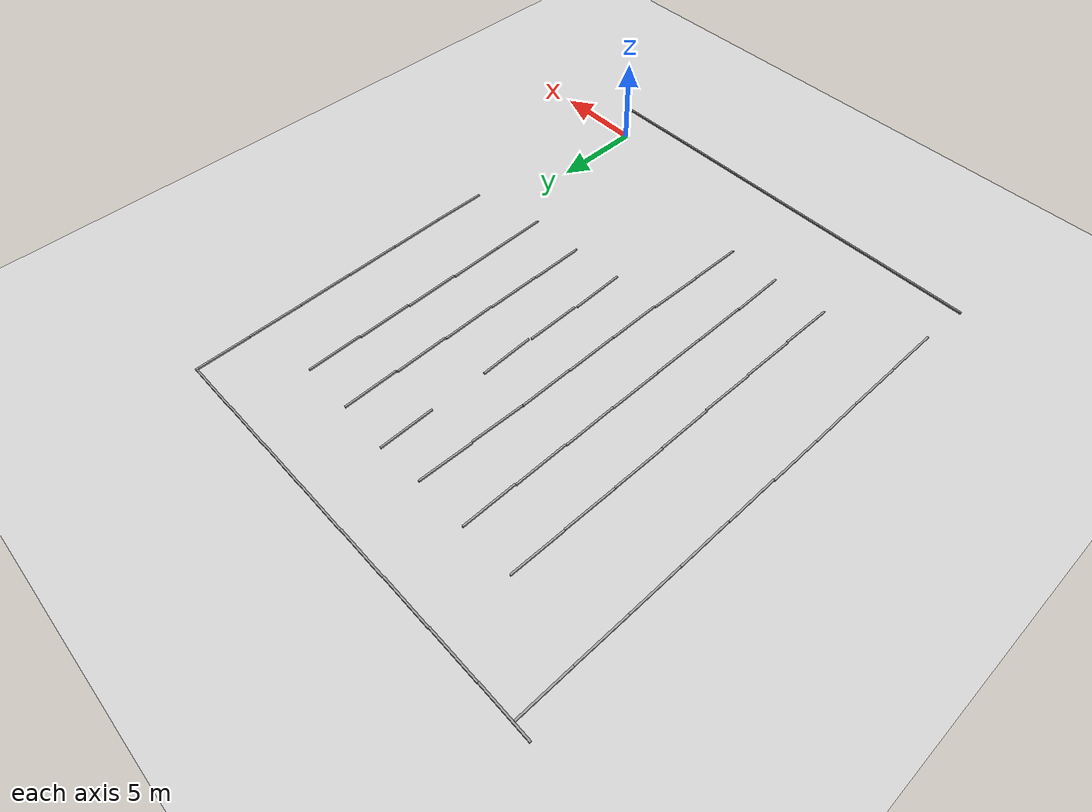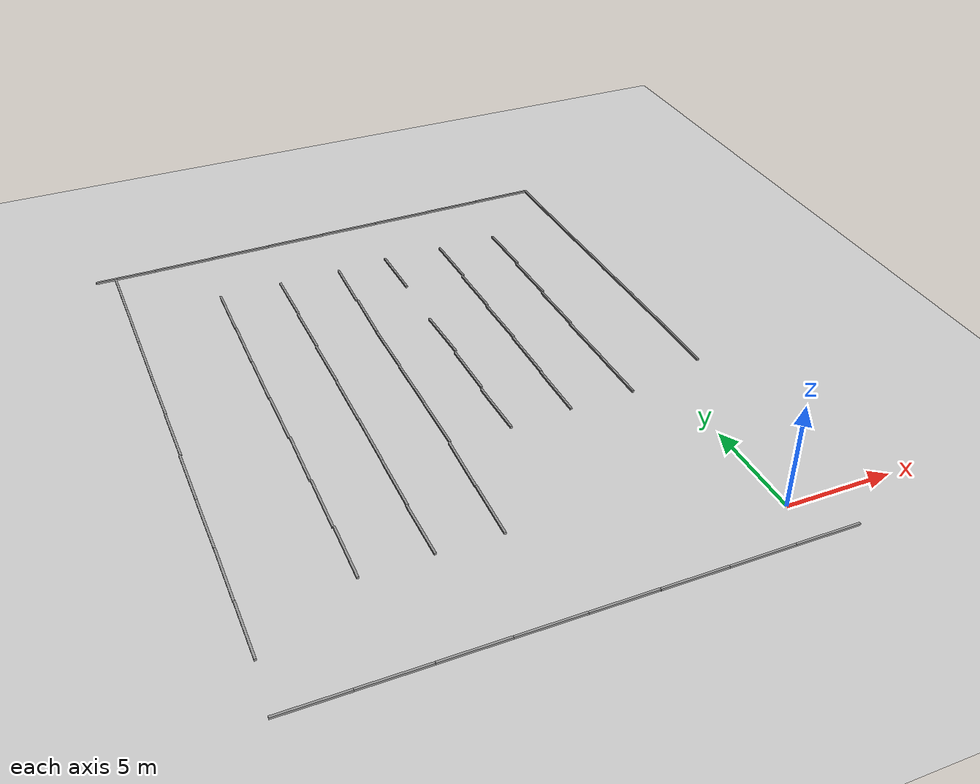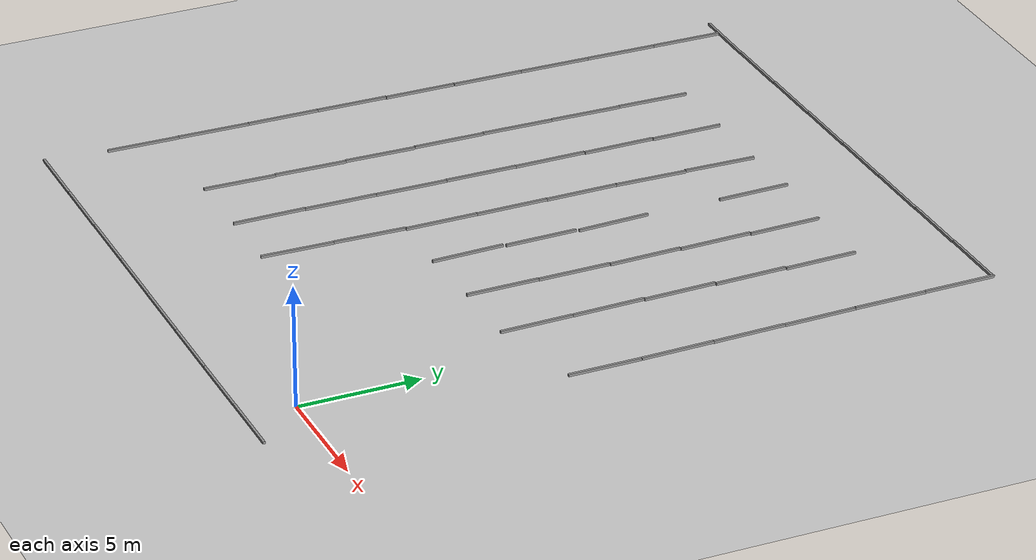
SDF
<sdf version="1.6">
 <world name="default">
  <light name="sun" type="directional">
   <pose>0 0 10 0 -0 0</pose>
   <diffuse>0.8 0.8 0.8 1</diffuse>
   <specular>0.2 0.2 0.2 1</specular>
   <attenuation>
    <range>1000</range>
    <constant>0.9</constant>
    <linear>0.01</linear>
    <quadratic>0.001</quadratic>
   </attenuation>
   <direction>-0.5 0.1 -0.9</direction>
  </light>
  <model name="ground_plane">
   <static>1</static>
   <link name="link">
    <collision name="collision">
     <geometry><plane><normal>0 0 1</normal><size>100 100</size></plane></geometry>
     <surface>
      <contact><collide_bitmask>65535</collide_bitmask></contact>
      <friction><ode><mu>100</mu><mu2>50</mu2></ode></friction>
     </surface>
    </collision>
    <visual name="visual">
     <cast_shadows>0</cast_shadows>
     <geometry><plane><normal>0 0 1</normal><size>100 100</size></plane></geometry>
     <material>
      <script><uri>file://media/materials/scripts/gazebo.material</uri><name>Gazebo/Grey</name></script>
     </material>
    </visual>
   </link>
  </model>
  <gravity>0 0 -9.8</gravity>
  <magnetic_field>6e-06 2.3e-05 -4.2e-05</magnetic_field>
  <atmosphere type="adiabatic"/>
  <physics name="default_physics" default="0" type="ode">
   <max_step_size>0.001</max_step_size>
   <real_time_factor>1</real_time_factor>
   <real_time_update_rate>1000</real_time_update_rate>
  </physics>
  <scene><ambient>0.4 0.4 0.4 1</ambient><background>0.7 0.7 0.7 1</background><shadows>1</shadows></scene>
  <audio><device>default</device></audio>
  <spherical_coordinates>
   <surface_model>EARTH_WGS84</surface_model>
   <latitude_deg>0</latitude_deg>
   <longitude_deg>0</longitude_deg>
   <elevation>0</elevation>
   <heading_deg>0</heading_deg>
  </spherical_coordinates>
  <model name="ruler_y">
   <link name="link_2">
    <inertial>
     <mass>1</mass>
     <inertia>
      <ixx>0.166667</ixx>
      <ixy>0</ixy>
      <ixz>0</ixz>
      <iyy>0.166667</iyy>
      <iyz>0</iyz>
      <izz>0.166667</izz>
     </inertia>
    </inertial>
    <visual name="visual">
     <geometry><box><size>0.1 3 0.1</size></box></geometry>
     <material>
      <lighting>1</lighting>
      <script><uri>file://media/materials/scripts/gazebo.material</uri><name>Gazebo/Grey</name></script>
      <shader type="vertex"><normal_map>__default__</normal_map></shader>
      <ambient>0.3 0.3 0.3 1</ambient>
      <diffuse>0.7 0.7 0.7 1</diffuse>
      <specular>0.01 0.01 0.01 1</specular>
      <emissive>0 0 0 1</emissive>
     </material>
    </visual>
    <collision name="collision">
     <geometry><box><size>0.1 3 0.1</size></box></geometry>
     <surface>
      <friction>
       <ode><mu>1</mu><mu2>1</mu2><fdir1>0 0 0</fdir1><slip1>0</slip1><slip2>0</slip2></ode>
       <torsional>
        <coefficient>1</coefficient>
        <patch_radius>0</patch_radius>
        <surface_radius>0</surface_radius>
        <use_patch_radius>1</use_patch_radius>
        <ode><slip>0</slip></ode>
       </torsional>
      </friction>
      <bounce><restitution_coefficient>0</restitution_coefficient><threshold>1e+06</threshold></bounce>
      <contact>
       <collide_without_contact>0</collide_without_contact>
       <collide_without_contact_bitmask>1</collide_without_contact_bitmask>
       <collide_bitmask>1</collide_bitmask>
       <ode>
        <soft_cfm>0</soft_cfm>
        <soft_erp>0.2</soft_erp>
        <kp>1e+13</kp>
        <kd>1</kd>
        <max_vel>0.01</max_vel>
        <min_depth>0</min_depth>
       </ode>
       <bullet>
        <split_impulse>1</split_impulse>
        <split_impulse_penetration_threshold>-0.01</split_impulse_penetration_threshold>
        <soft_cfm>0</soft_cfm>
        <soft_erp>0.2</soft_erp>
        <kp>1e+13</kp>
        <kd>1</kd>
       </bullet>
      </contact>
     </surface>
    </collision>
   </link>
   <static>0</static>
   <plugin name="ruler_y" filename="ruler_y"/>
   <pose>-1.97709 10.5171 0.049602 0.000266 -6e-06 0.022572</pose>
  </model>
  <model name="ruler_y_clone">
   <link name="link_2">
    <inertial>
     <mass>1</mass>
     <inertia>
      <ixx>0.166667</ixx>
      <ixy>0</ixy>
      <ixz>0</ixz>
      <iyy>0.166667</iyy>
      <iyz>0</iyz>
      <izz>0.166667</izz>
     </inertia>
    </inertial>
    <visual name="visual">
     <geometry><box><size>0.1 3 0.1</size></box></geometry>
     <material>
      <lighting>1</lighting>
      <script><uri>file://media/materials/scripts/gazebo.material</uri><name>Gazebo/Grey</name></script>
      <shader type="vertex"><normal_map>__default__</normal_map></shader>
      <ambient>0.3 0.3 0.3 1</ambient>
      <diffuse>0.7 0.7 0.7 1</diffuse>
      <specular>0.01 0.01 0.01 1</specular>
      <emissive>0 0 0 1</emissive>
     </material>
    </visual>
    <collision name="collision">
     <geometry><box><size>0.1 3 0.1</size></box></geometry>
     <surface>
      <friction>
       <ode><mu>1</mu><mu2>1</mu2><fdir1>0 0 0</fdir1><slip1>0</slip1><slip2>0</slip2></ode>
       <torsional>
        <coefficient>1</coefficient>
        <patch_radius>0</patch_radius>
        <surface_radius>0</surface_radius>
        <use_patch_radius>1</use_patch_radius>
        <ode><slip>0</slip></ode>
       </torsional>
      </friction>
      <bounce><restitution_coefficient>0</restitution_coefficient><threshold>1e+06</threshold></bounce>
      <contact>
       <collide_without_contact>0</collide_without_contact>
       <collide_without_contact_bitmask>1</collide_without_contact_bitmask>
       <collide_bitmask>1</collide_bitmask>
       <ode>
        <soft_cfm>0</soft_cfm>
        <soft_erp>0.2</soft_erp>
        <kp>1e+13</kp>
        <kd>1</kd>
        <max_vel>0.01</max_vel>
        <min_depth>0</min_depth>
       </ode>
       <bullet>
        <split_impulse>1</split_impulse>
        <split_impulse_penetration_threshold>-0.01</split_impulse_penetration_threshold>
        <soft_cfm>0</soft_cfm>
        <soft_erp>0.2</soft_erp>
        <kp>1e+13</kp>
        <kd>1</kd>
       </bullet>
      </contact>
     </surface>
    </collision>
   </link>
   <static>0</static>
   <plugin name="ruler_y" filename="ruler_y"/>
   <pose>-2.04061 13.5167 0.049602 -0.000266 -6e-06 0.027159</pose>
  </model>
  <model name="ruler_y_clone_clone">
   <link name="link_2">
    <inertial>
     <mass>1</mass>
     <inertia>
      <ixx>0.166667</ixx>
      <ixy>0</ixy>
      <ixz>0</ixz>
      <iyy>0.166667</iyy>
      <iyz>0</iyz>
      <izz>0.166667</izz>
     </inertia>
    </inertial>
    <visual name="visual">
     <geometry><box><size>0.1 3 0.1</size></box></geometry>
     <material>
      <lighting>1</lighting>
      <script><uri>file://media/materials/scripts/gazebo.material</uri><name>Gazebo/Grey</name></script>
      <shader type="vertex"><normal_map>__default__</normal_map></shader>
      <ambient>0.3 0.3 0.3 1</ambient>
      <diffuse>0.7 0.7 0.7 1</diffuse>
      <specular>0.01 0.01 0.01 1</specular>
      <emissive>0 0 0 1</emissive>
     </material>
    </visual>
    <collision name="collision">
     <geometry><box><size>0.1 3 0.1</size></box></geometry>
     <surface>
      <friction>
       <ode><mu>1</mu><mu2>1</mu2><fdir1>0 0 0</fdir1><slip1>0</slip1><slip2>0</slip2></ode>
       <torsional>
        <coefficient>1</coefficient>
        <patch_radius>0</patch_radius>
        <surface_radius>0</surface_radius>
        <use_patch_radius>1</use_patch_radius>
        <ode><slip>0</slip></ode>
       </torsional>
      </friction>
      <bounce><restitution_coefficient>0</restitution_coefficient><threshold>1e+06</threshold></bounce>
      <contact>
       <collide_without_contact>0</collide_without_contact>
       <collide_without_contact_bitmask>1</collide_without_contact_bitmask>
       <collide_bitmask>1</collide_bitmask>
       <ode>
        <soft_cfm>0</soft_cfm>
        <soft_erp>0.2</soft_erp>
        <kp>1e+13</kp>
        <kd>1</kd>
        <max_vel>0.01</max_vel>
        <min_depth>0</min_depth>
       </ode>
       <bullet>
        <split_impulse>1</split_impulse>
        <split_impulse_penetration_threshold>-0.01</split_impulse_penetration_threshold>
        <soft_cfm>0</soft_cfm>
        <soft_erp>0.2</soft_erp>
        <kp>1e+13</kp>
        <kd>1</kd>
       </bullet>
      </contact>
     </surface>
    </collision>
   </link>
   <static>0</static>
   <plugin name="ruler_y" filename="ruler_y"/>
   <pose>-2.05827 16.5173 0.049602 0.000266 5e-06 0.025433</pose>
  </model>
  <model name="ruler_y_clone_clone_clone">
   <link name="link_2">
    <inertial>
     <mass>1</mass>
     <inertia>
      <ixx>0.166667</ixx>
      <ixy>0</ixy>
      <ixz>0</ixz>
      <iyy>0.166667</iyy>
      <iyz>0</iyz>
      <izz>0.166667</izz>
     </inertia>
    </inertial>
    <visual name="visual">
     <geometry><box><size>0.1 3 0.1</size></box></geometry>
     <material>
      <lighting>1</lighting>
      <script><uri>file://media/materials/scripts/gazebo.material</uri><name>Gazebo/Grey</name></script>
      <shader type="vertex"><normal_map>__default__</normal_map></shader>
      <ambient>0.3 0.3 0.3 1</ambient>
      <diffuse>0.7 0.7 0.7 1</diffuse>
      <specular>0.01 0.01 0.01 1</specular>
      <emissive>0 0 0 1</emissive>
     </material>
    </visual>
    <collision name="collision">
     <geometry><box><size>0.1 3 0.1</size></box></geometry>
     <surface>
      <friction>
       <ode><mu>1</mu><mu2>1</mu2><fdir1>0 0 0</fdir1><slip1>0</slip1><slip2>0</slip2></ode>
       <torsional>
        <coefficient>1</coefficient>
        <patch_radius>0</patch_radius>
        <surface_radius>0</surface_radius>
        <use_patch_radius>1</use_patch_radius>
        <ode><slip>0</slip></ode>
       </torsional>
      </friction>
      <bounce><restitution_coefficient>0</restitution_coefficient><threshold>1e+06</threshold></bounce>
      <contact>
       <collide_without_contact>0</collide_without_contact>
       <collide_without_contact_bitmask>1</collide_without_contact_bitmask>
       <collide_bitmask>1</collide_bitmask>
       <ode>
        <soft_cfm>0</soft_cfm>
        <soft_erp>0.2</soft_erp>
        <kp>1e+13</kp>
        <kd>1</kd>
        <max_vel>0.01</max_vel>
        <min_depth>0</min_depth>
       </ode>
       <bullet>
        <split_impulse>1</split_impulse>
        <split_impulse_penetration_threshold>-0.01</split_impulse_penetration_threshold>
        <soft_cfm>0</soft_cfm>
        <soft_erp>0.2</soft_erp>
        <kp>1e+13</kp>
        <kd>1</kd>
       </bullet>
      </contact>
     </surface>
    </collision>
   </link>
   <static>0</static>
   <plugin name="ruler_y" filename="ruler_y"/>
   <pose>-2.05869 19.5258 0.049602 -0.000266 6e-06 0.02639</pose>
  </model>
  <model name="ruler_y_clone_clone_clone_clone">
   <link name="link_2">
    <inertial>
     <mass>1</mass>
     <inertia>
      <ixx>0.166667</ixx>
      <ixy>0</ixy>
      <ixz>0</ixz>
      <iyy>0.166667</iyy>
      <iyz>0</iyz>
      <izz>0.166667</izz>
     </inertia>
    </inertial>
    <visual name="visual">
     <geometry><box><size>0.1 3 0.1</size></box></geometry>
     <material>
      <lighting>1</lighting>
      <script><uri>file://media/materials/scripts/gazebo.material</uri><name>Gazebo/Grey</name></script>
      <shader type="vertex"><normal_map>__default__</normal_map></shader>
      <ambient>0.3 0.3 0.3 1</ambient>
      <diffuse>0.7 0.7 0.7 1</diffuse>
      <specular>0.01 0.01 0.01 1</specular>
      <emissive>0 0 0 1</emissive>
     </material>
    </visual>
    <collision name="collision">
     <geometry><box><size>0.1 3 0.1</size></box></geometry>
     <surface>
      <friction>
       <ode><mu>1</mu><mu2>1</mu2><fdir1>0 0 0</fdir1><slip1>0</slip1><slip2>0</slip2></ode>
       <torsional>
        <coefficient>1</coefficient>
        <patch_radius>0</patch_radius>
        <surface_radius>0</surface_radius>
        <use_patch_radius>1</use_patch_radius>
        <ode><slip>0</slip></ode>
       </torsional>
      </friction>
      <bounce><restitution_coefficient>0</restitution_coefficient><threshold>1e+06</threshold></bounce>
      <contact>
       <collide_without_contact>0</collide_without_contact>
       <collide_without_contact_bitmask>1</collide_without_contact_bitmask>
       <collide_bitmask>1</collide_bitmask>
       <ode>
        <soft_cfm>0</soft_cfm>
        <soft_erp>0.2</soft_erp>
        <kp>1e+13</kp>
        <kd>1</kd>
        <max_vel>0.01</max_vel>
        <min_depth>0</min_depth>
       </ode>
       <bullet>
        <split_impulse>1</split_impulse>
        <split_impulse_penetration_threshold>-0.01</split_impulse_penetration_threshold>
        <soft_cfm>0</soft_cfm>
        <soft_erp>0.2</soft_erp>
        <kp>1e+13</kp>
        <kd>1</kd>
       </bullet>
      </contact>
     </surface>
    </collision>
   </link>
   <static>0</static>
   <plugin name="ruler_y" filename="ruler_y"/>
   <pose>-2.06494 22.5275 0.049602 -0.000266 6e-06 0.026388</pose>
  </model>
  <model name="ruler_y_clone_0">
   <link name="link_2">
    <inertial>
     <mass>1</mass>
     <inertia>
      <ixx>0.166667</ixx>
      <ixy>0</ixy>
      <ixz>0</ixz>
      <iyy>0.166667</iyy>
      <iyz>0</iyz>
      <izz>0.166667</izz>
     </inertia>
    </inertial>
    <visual name="visual">
     <geometry><box><size>0.1 3 0.1</size></box></geometry>
     <material>
      <lighting>1</lighting>
      <script><uri>file://media/materials/scripts/gazebo.material</uri><name>Gazebo/Grey</name></script>
      <shader type="vertex"><normal_map>__default__</normal_map></shader>
      <ambient>0.3 0.3 0.3 1</ambient>
      <diffuse>0.7 0.7 0.7 1</diffuse>
      <specular>0.01 0.01 0.01 1</specular>
      <emissive>0 0 0 1</emissive>
     </material>
    </visual>
    <collision name="collision">
     <geometry><box><size>0.1 3 0.1</size></box></geometry>
     <surface>
      <friction>
       <ode><mu>1</mu><mu2>1</mu2><fdir1>0 0 0</fdir1><slip1>0</slip1><slip2>0</slip2></ode>
       <torsional>
        <coefficient>1</coefficient>
        <patch_radius>0</patch_radius>
        <surface_radius>0</surface_radius>
        <use_patch_radius>1</use_patch_radius>
        <ode><slip>0</slip></ode>
       </torsional>
      </friction>
      <bounce><restitution_coefficient>0</restitution_coefficient><threshold>1e+06</threshold></bounce>
      <contact>
       <collide_without_contact>0</collide_without_contact>
       <collide_without_contact_bitmask>1</collide_without_contact_bitmask>
       <collide_bitmask>1</collide_bitmask>
       <ode>
        <soft_cfm>0</soft_cfm>
        <soft_erp>0.2</soft_erp>
        <kp>1e+13</kp>
        <kd>1</kd>
        <max_vel>0.01</max_vel>
        <min_depth>0</min_depth>
       </ode>
       <bullet>
        <split_impulse>1</split_impulse>
        <split_impulse_penetration_threshold>-0.01</split_impulse_penetration_threshold>
        <soft_cfm>0</soft_cfm>
        <soft_erp>0.2</soft_erp>
        <kp>1e+13</kp>
        <kd>1</kd>
       </bullet>
      </contact>
     </surface>
    </collision>
   </link>
   <static>0</static>
   <plugin name="ruler_y" filename="ruler_y"/>
   <pose>-5.0857 10.4839 0.049602 -0.000266 -6e-06 0.009055</pose>
  </model>
  <model name="ruler_y_clone_0_clone">
   <link name="link_2">
    <inertial>
     <mass>1</mass>
     <inertia>
      <ixx>0.166667</ixx>
      <ixy>0</ixy>
      <ixz>0</ixz>
      <iyy>0.166667</iyy>
      <iyz>0</iyz>
      <izz>0.166667</izz>
     </inertia>
    </inertial>
    <visual name="visual">
     <geometry><box><size>0.1 3 0.1</size></box></geometry>
     <material>
      <lighting>1</lighting>
      <script><uri>file://media/materials/scripts/gazebo.material</uri><name>Gazebo/Grey</name></script>
      <shader type="vertex"><normal_map>__default__</normal_map></shader>
      <ambient>0.3 0.3 0.3 1</ambient>
      <diffuse>0.7 0.7 0.7 1</diffuse>
      <specular>0.01 0.01 0.01 1</specular>
      <emissive>0 0 0 1</emissive>
     </material>
    </visual>
    <collision name="collision">
     <geometry><box><size>0.1 3 0.1</size></box></geometry>
     <surface>
      <friction>
       <ode><mu>1</mu><mu2>1</mu2><fdir1>0 0 0</fdir1><slip1>0</slip1><slip2>0</slip2></ode>
       <torsional>
        <coefficient>1</coefficient>
        <patch_radius>0</patch_radius>
        <surface_radius>0</surface_radius>
        <use_patch_radius>1</use_patch_radius>
        <ode><slip>0</slip></ode>
       </torsional>
      </friction>
      <bounce><restitution_coefficient>0</restitution_coefficient><threshold>1e+06</threshold></bounce>
      <contact>
       <collide_without_contact>0</collide_without_contact>
       <collide_without_contact_bitmask>1</collide_without_contact_bitmask>
       <collide_bitmask>1</collide_bitmask>
       <ode>
        <soft_cfm>0</soft_cfm>
        <soft_erp>0.2</soft_erp>
        <kp>1e+13</kp>
        <kd>1</kd>
        <max_vel>0.01</max_vel>
        <min_depth>0</min_depth>
       </ode>
       <bullet>
        <split_impulse>1</split_impulse>
        <split_impulse_penetration_threshold>-0.01</split_impulse_penetration_threshold>
        <soft_cfm>0</soft_cfm>
        <soft_erp>0.2</soft_erp>
        <kp>1e+13</kp>
        <kd>1</kd>
       </bullet>
      </contact>
     </surface>
    </collision>
   </link>
   <static>0</static>
   <plugin name="ruler_y" filename="ruler_y"/>
   <pose>-5.08241 13.4844 0.049602 0.000266 6e-06 0.009093</pose>
  </model>
  <model name="ruler_y_clone_0_clone_clone">
   <link name="link_2">
    <inertial>
     <mass>1</mass>
     <inertia>
      <ixx>0.166667</ixx>
      <ixy>0</ixy>
      <ixz>0</ixz>
      <iyy>0.166667</iyy>
      <iyz>0</iyz>
      <izz>0.166667</izz>
     </inertia>
    </inertial>
    <visual name="visual">
     <geometry><box><size>0.1 3 0.1</size></box></geometry>
     <material>
      <lighting>1</lighting>
      <script><uri>file://media/materials/scripts/gazebo.material</uri><name>Gazebo/Grey</name></script>
      <shader type="vertex"><normal_map>__default__</normal_map></shader>
      <ambient>0.3 0.3 0.3 1</ambient>
      <diffuse>0.7 0.7 0.7 1</diffuse>
      <specular>0.01 0.01 0.01 1</specular>
      <emissive>0 0 0 1</emissive>
     </material>
    </visual>
    <collision name="collision">
     <geometry><box><size>0.1 3 0.1</size></box></geometry>
     <surface>
      <friction>
       <ode><mu>1</mu><mu2>1</mu2><fdir1>0 0 0</fdir1><slip1>0</slip1><slip2>0</slip2></ode>
       <torsional>
        <coefficient>1</coefficient>
        <patch_radius>0</patch_radius>
        <surface_radius>0</surface_radius>
        <use_patch_radius>1</use_patch_radius>
        <ode><slip>0</slip></ode>
       </torsional>
      </friction>
      <bounce><restitution_coefficient>0</restitution_coefficient><threshold>1e+06</threshold></bounce>
      <contact>
       <collide_without_contact>0</collide_without_contact>
       <collide_without_contact_bitmask>1</collide_without_contact_bitmask>
       <collide_bitmask>1</collide_bitmask>
       <ode>
        <soft_cfm>0</soft_cfm>
        <soft_erp>0.2</soft_erp>
        <kp>1e+13</kp>
        <kd>1</kd>
        <max_vel>0.01</max_vel>
        <min_depth>0</min_depth>
       </ode>
       <bullet>
        <split_impulse>1</split_impulse>
        <split_impulse_penetration_threshold>-0.01</split_impulse_penetration_threshold>
        <soft_cfm>0</soft_cfm>
        <soft_erp>0.2</soft_erp>
        <kp>1e+13</kp>
        <kd>1</kd>
       </bullet>
      </contact>
     </surface>
    </collision>
   </link>
   <static>0</static>
   <plugin name="ruler_y" filename="ruler_y"/>
   <pose>-5.09137 16.4888 0.049602 -0.000266 6e-06 0.026108</pose>
  </model>
  <model name="ruler_y_clone_0_clone_clone_clone">
   <link name="link_2">
    <inertial>
     <mass>1</mass>
     <inertia>
      <ixx>0.166667</ixx>
      <ixy>0</ixy>
      <ixz>0</ixz>
      <iyy>0.166667</iyy>
      <iyz>0</iyz>
      <izz>0.166667</izz>
     </inertia>
    </inertial>
    <visual name="visual">
     <geometry><box><size>0.1 3 0.1</size></box></geometry>
     <material>
      <lighting>1</lighting>
      <script><uri>file://media/materials/scripts/gazebo.material</uri><name>Gazebo/Grey</name></script>
      <shader type="vertex"><normal_map>__default__</normal_map></shader>
      <ambient>0.3 0.3 0.3 1</ambient>
      <diffuse>0.7 0.7 0.7 1</diffuse>
      <specular>0.01 0.01 0.01 1</specular>
      <emissive>0 0 0 1</emissive>
     </material>
    </visual>
    <collision name="collision">
     <geometry><box><size>0.1 3 0.1</size></box></geometry>
     <surface>
      <friction>
       <ode><mu>1</mu><mu2>1</mu2><fdir1>0 0 0</fdir1><slip1>0</slip1><slip2>0</slip2></ode>
       <torsional>
        <coefficient>1</coefficient>
        <patch_radius>0</patch_radius>
        <surface_radius>0</surface_radius>
        <use_patch_radius>1</use_patch_radius>
        <ode><slip>0</slip></ode>
       </torsional>
      </friction>
      <bounce><restitution_coefficient>0</restitution_coefficient><threshold>1e+06</threshold></bounce>
      <contact>
       <collide_without_contact>0</collide_without_contact>
       <collide_without_contact_bitmask>1</collide_without_contact_bitmask>
       <collide_bitmask>1</collide_bitmask>
       <ode>
        <soft_cfm>0</soft_cfm>
        <soft_erp>0.2</soft_erp>
        <kp>1e+13</kp>
        <kd>1</kd>
        <max_vel>0.01</max_vel>
        <min_depth>0</min_depth>
       </ode>
       <bullet>
        <split_impulse>1</split_impulse>
        <split_impulse_penetration_threshold>-0.01</split_impulse_penetration_threshold>
        <soft_cfm>0</soft_cfm>
        <soft_erp>0.2</soft_erp>
        <kp>1e+13</kp>
        <kd>1</kd>
       </bullet>
      </contact>
     </surface>
    </collision>
   </link>
   <static>0</static>
   <plugin name="ruler_y" filename="ruler_y"/>
   <pose>-5.10693 19.5041 0.049602 -0.000266 6e-06 0.026106</pose>
  </model>
  <model name="ruler_y_clone_0_clone_clone_clone_clone">
   <link name="link_2">
    <inertial>
     <mass>1</mass>
     <inertia>
      <ixx>0.166667</ixx>
      <ixy>0</ixy>
      <ixz>0</ixz>
      <iyy>0.166667</iyy>
      <iyz>0</iyz>
      <izz>0.166667</izz>
     </inertia>
    </inertial>
    <visual name="visual">
     <geometry><box><size>0.1 3 0.1</size></box></geometry>
     <material>
      <lighting>1</lighting>
      <script><uri>file://media/materials/scripts/gazebo.material</uri><name>Gazebo/Grey</name></script>
      <shader type="vertex"><normal_map>__default__</normal_map></shader>
      <ambient>0.3 0.3 0.3 1</ambient>
      <diffuse>0.7 0.7 0.7 1</diffuse>
      <specular>0.01 0.01 0.01 1</specular>
      <emissive>0 0 0 1</emissive>
     </material>
    </visual>
    <collision name="collision">
     <geometry><box><size>0.1 3 0.1</size></box></geometry>
     <surface>
      <friction>
       <ode><mu>1</mu><mu2>1</mu2><fdir1>0 0 0</fdir1><slip1>0</slip1><slip2>0</slip2></ode>
       <torsional>
        <coefficient>1</coefficient>
        <patch_radius>0</patch_radius>
        <surface_radius>0</surface_radius>
        <use_patch_radius>1</use_patch_radius>
        <ode><slip>0</slip></ode>
       </torsional>
      </friction>
      <bounce><restitution_coefficient>0</restitution_coefficient><threshold>1e+06</threshold></bounce>
      <contact>
       <collide_without_contact>0</collide_without_contact>
       <collide_without_contact_bitmask>1</collide_without_contact_bitmask>
       <collide_bitmask>1</collide_bitmask>
       <ode>
        <soft_cfm>0</soft_cfm>
        <soft_erp>0.2</soft_erp>
        <kp>1e+13</kp>
        <kd>1</kd>
        <max_vel>0.01</max_vel>
        <min_depth>0</min_depth>
       </ode>
       <bullet>
        <split_impulse>1</split_impulse>
        <split_impulse_penetration_threshold>-0.01</split_impulse_penetration_threshold>
        <soft_cfm>0</soft_cfm>
        <soft_erp>0.2</soft_erp>
        <kp>1e+13</kp>
        <kd>1</kd>
       </bullet>
      </contact>
     </surface>
    </collision>
   </link>
   <static>0</static>
   <plugin name="ruler_y" filename="ruler_y"/>
   <pose>-5.11291 22.5117 0.049602 0.000266 -6e-06 0.026104</pose>
  </model>
  <model name="ruler_y_clone_0_clone_0">
   <link name="link_2">
    <inertial>
     <mass>1</mass>
     <inertia>
      <ixx>0.166667</ixx>
      <ixy>0</ixy>
      <ixz>0</ixz>
      <iyy>0.166667</iyy>
      <iyz>0</iyz>
      <izz>0.166667</izz>
     </inertia>
    </inertial>
    <visual name="visual">
     <geometry><box><size>0.1 3 0.1</size></box></geometry>
     <material>
      <lighting>1</lighting>
      <script><uri>file://media/materials/scripts/gazebo.material</uri><name>Gazebo/Grey</name></script>
      <shader type="vertex"><normal_map>__default__</normal_map></shader>
      <ambient>0.3 0.3 0.3 1</ambient>
      <diffuse>0.7 0.7 0.7 1</diffuse>
      <specular>0.01 0.01 0.01 1</specular>
      <emissive>0 0 0 1</emissive>
     </material>
    </visual>
    <collision name="collision">
     <geometry><box><size>0.1 3 0.1</size></box></geometry>
     <surface>
      <friction>
       <ode><mu>1</mu><mu2>1</mu2><fdir1>0 0 0</fdir1><slip1>0</slip1><slip2>0</slip2></ode>
       <torsional>
        <coefficient>1</coefficient>
        <patch_radius>0</patch_radius>
        <surface_radius>0</surface_radius>
        <use_patch_radius>1</use_patch_radius>
        <ode><slip>0</slip></ode>
       </torsional>
      </friction>
      <bounce><restitution_coefficient>0</restitution_coefficient><threshold>1e+06</threshold></bounce>
      <contact>
       <collide_without_contact>0</collide_without_contact>
       <collide_without_contact_bitmask>1</collide_without_contact_bitmask>
       <collide_bitmask>1</collide_bitmask>
       <ode>
        <soft_cfm>0</soft_cfm>
        <soft_erp>0.2</soft_erp>
        <kp>1e+13</kp>
        <kd>1</kd>
        <max_vel>0.01</max_vel>
        <min_depth>0</min_depth>
       </ode>
       <bullet>
        <split_impulse>1</split_impulse>
        <split_impulse_penetration_threshold>-0.01</split_impulse_penetration_threshold>
        <soft_cfm>0</soft_cfm>
        <soft_erp>0.2</soft_erp>
        <kp>1e+13</kp>
        <kd>1</kd>
       </bullet>
      </contact>
     </surface>
    </collision>
   </link>
   <static>0</static>
   <plugin name="ruler_y" filename="ruler_y"/>
   <pose>-8.08134 10.3316 0.049602 0.000266 -6e-06 0.030176</pose>
  </model>
  <model name="ruler_y_clone_0_clone_0_clone">
   <link name="link_2">
    <inertial>
     <mass>1</mass>
     <inertia>
      <ixx>0.166667</ixx>
      <ixy>0</ixy>
      <ixz>0</ixz>
      <iyy>0.166667</iyy>
      <iyz>0</iyz>
      <izz>0.166667</izz>
     </inertia>
    </inertial>
    <visual name="visual">
     <geometry><box><size>0.1 3 0.1</size></box></geometry>
     <material>
      <lighting>1</lighting>
      <script><uri>file://media/materials/scripts/gazebo.material</uri><name>Gazebo/Grey</name></script>
      <shader type="vertex"><normal_map>__default__</normal_map></shader>
      <ambient>0.3 0.3 0.3 1</ambient>
      <diffuse>0.7 0.7 0.7 1</diffuse>
      <specular>0.01 0.01 0.01 1</specular>
      <emissive>0 0 0 1</emissive>
     </material>
    </visual>
    <collision name="collision">
     <geometry><box><size>0.1 3 0.1</size></box></geometry>
     <surface>
      <friction>
       <ode><mu>1</mu><mu2>1</mu2><fdir1>0 0 0</fdir1><slip1>0</slip1><slip2>0</slip2></ode>
       <torsional>
        <coefficient>1</coefficient>
        <patch_radius>0</patch_radius>
        <surface_radius>0</surface_radius>
        <use_patch_radius>1</use_patch_radius>
        <ode><slip>0</slip></ode>
       </torsional>
      </friction>
      <bounce><restitution_coefficient>0</restitution_coefficient><threshold>1e+06</threshold></bounce>
      <contact>
       <collide_without_contact>0</collide_without_contact>
       <collide_without_contact_bitmask>1</collide_without_contact_bitmask>
       <collide_bitmask>1</collide_bitmask>
       <ode>
        <soft_cfm>0</soft_cfm>
        <soft_erp>0.2</soft_erp>
        <kp>1e+13</kp>
        <kd>1</kd>
        <max_vel>0.01</max_vel>
        <min_depth>0</min_depth>
       </ode>
       <bullet>
        <split_impulse>1</split_impulse>
        <split_impulse_penetration_threshold>-0.01</split_impulse_penetration_threshold>
        <soft_cfm>0</soft_cfm>
        <soft_erp>0.2</soft_erp>
        <kp>1e+13</kp>
        <kd>1</kd>
       </bullet>
      </contact>
     </surface>
    </collision>
   </link>
   <static>0</static>
   <plugin name="ruler_y" filename="ruler_y"/>
   <pose>-8.07804 13.4371 0.049602 0.000266 -6e-06 0.015407</pose>
  </model>
  <model name="ruler_y_clone_0_clone_0_clone_clone">
   <link name="link_2">
    <inertial>
     <mass>1</mass>
     <inertia>
      <ixx>0.166667</ixx>
      <ixy>0</ixy>
      <ixz>0</ixz>
      <iyy>0.166667</iyy>
      <iyz>0</iyz>
      <izz>0.166667</izz>
     </inertia>
    </inertial>
    <visual name="visual">
     <geometry><box><size>0.1 3 0.1</size></box></geometry>
     <material>
      <lighting>1</lighting>
      <script><uri>file://media/materials/scripts/gazebo.material</uri><name>Gazebo/Grey</name></script>
      <shader type="vertex"><normal_map>__default__</normal_map></shader>
      <ambient>0.3 0.3 0.3 1</ambient>
      <diffuse>0.7 0.7 0.7 1</diffuse>
      <specular>0.01 0.01 0.01 1</specular>
      <emissive>0 0 0 1</emissive>
     </material>
    </visual>
    <collision name="collision">
     <geometry><box><size>0.1 3 0.1</size></box></geometry>
     <surface>
      <friction>
       <ode><mu>1</mu><mu2>1</mu2><fdir1>0 0 0</fdir1><slip1>0</slip1><slip2>0</slip2></ode>
       <torsional>
        <coefficient>1</coefficient>
        <patch_radius>0</patch_radius>
        <surface_radius>0</surface_radius>
        <use_patch_radius>1</use_patch_radius>
        <ode><slip>0</slip></ode>
       </torsional>
      </friction>
      <bounce><restitution_coefficient>0</restitution_coefficient><threshold>1e+06</threshold></bounce>
      <contact>
       <collide_without_contact>0</collide_without_contact>
       <collide_without_contact_bitmask>1</collide_without_contact_bitmask>
       <collide_bitmask>1</collide_bitmask>
       <ode>
        <soft_cfm>0</soft_cfm>
        <soft_erp>0.2</soft_erp>
        <kp>1e+13</kp>
        <kd>1</kd>
        <max_vel>0.01</max_vel>
        <min_depth>0</min_depth>
       </ode>
       <bullet>
        <split_impulse>1</split_impulse>
        <split_impulse_penetration_threshold>-0.01</split_impulse_penetration_threshold>
        <soft_cfm>0</soft_cfm>
        <soft_erp>0.2</soft_erp>
        <kp>1e+13</kp>
        <kd>1</kd>
       </bullet>
      </contact>
     </surface>
    </collision>
   </link>
   <static>0</static>
   <plugin name="ruler_y" filename="ruler_y"/>
   <pose>-8.08392 16.5381 0.049602 -0.000266 6e-06 0.04215</pose>
  </model>
  <model name="ruler_y_clone_0_clone_0_clone_clone_clone_clone">
   <link name="link_2">
    <inertial>
     <mass>1</mass>
     <inertia>
      <ixx>0.166667</ixx>
      <ixy>0</ixy>
      <ixz>0</ixz>
      <iyy>0.166667</iyy>
      <iyz>0</iyz>
      <izz>0.166667</izz>
     </inertia>
    </inertial>
    <visual name="visual">
     <geometry><box><size>0.1 3 0.1</size></box></geometry>
     <material>
      <lighting>1</lighting>
      <script><uri>file://media/materials/scripts/gazebo.material</uri><name>Gazebo/Grey</name></script>
      <shader type="vertex"><normal_map>__default__</normal_map></shader>
      <ambient>0.3 0.3 0.3 1</ambient>
      <diffuse>0.7 0.7 0.7 1</diffuse>
      <specular>0.01 0.01 0.01 1</specular>
      <emissive>0 0 0 1</emissive>
     </material>
    </visual>
    <collision name="collision">
     <geometry><box><size>0.1 3 0.1</size></box></geometry>
     <surface>
      <friction>
       <ode><mu>1</mu><mu2>1</mu2><fdir1>0 0 0</fdir1><slip1>0</slip1><slip2>0</slip2></ode>
       <torsional>
        <coefficient>1</coefficient>
        <patch_radius>0</patch_radius>
        <surface_radius>0</surface_radius>
        <use_patch_radius>1</use_patch_radius>
        <ode><slip>0</slip></ode>
       </torsional>
      </friction>
      <bounce><restitution_coefficient>0</restitution_coefficient><threshold>1e+06</threshold></bounce>
      <contact>
       <collide_without_contact>0</collide_without_contact>
       <collide_without_contact_bitmask>1</collide_without_contact_bitmask>
       <collide_bitmask>1</collide_bitmask>
       <ode>
        <soft_cfm>0</soft_cfm>
        <soft_erp>0.2</soft_erp>
        <kp>1e+13</kp>
        <kd>1</kd>
        <max_vel>0.01</max_vel>
        <min_depth>0</min_depth>
       </ode>
       <bullet>
        <split_impulse>1</split_impulse>
        <split_impulse_penetration_threshold>-0.01</split_impulse_penetration_threshold>
        <soft_cfm>0</soft_cfm>
        <soft_erp>0.2</soft_erp>
        <kp>1e+13</kp>
        <kd>1</kd>
       </bullet>
      </contact>
     </surface>
    </collision>
   </link>
   <static>0</static>
   <plugin name="ruler_y" filename="ruler_y"/>
   <pose>-8.1349 22.6445 0.049602 0.000266 -6e-06 0.02147</pose>
  </model>
  <model name="ruler_y_0">
   <link name="link_2">
    <inertial>
     <mass>1</mass>
     <inertia>
      <ixx>0.166667</ixx>
      <ixy>0</ixy>
      <ixz>0</ixz>
      <iyy>0.166667</iyy>
      <iyz>0</iyz>
      <izz>0.166667</izz>
     </inertia>
    </inertial>
    <visual name="visual">
     <geometry><box><size>0.1 3 0.1</size></box></geometry>
     <material>
      <lighting>1</lighting>
      <script><uri>file://media/materials/scripts/gazebo.material</uri><name>Gazebo/Grey</name></script>
      <shader type="vertex"><normal_map>__default__</normal_map></shader>
      <ambient>0.3 0.3 0.3 1</ambient>
      <diffuse>0.7 0.7 0.7 1</diffuse>
      <specular>0.01 0.01 0.01 1</specular>
      <emissive>0 0 0 1</emissive>
     </material>
    </visual>
    <collision name="collision">
     <geometry><box><size>0.1 3 0.1</size></box></geometry>
     <surface>
      <friction>
       <ode><mu>1</mu><mu2>1</mu2><fdir1>0 0 0</fdir1><slip1>0</slip1><slip2>0</slip2></ode>
       <torsional>
        <coefficient>1</coefficient>
        <patch_radius>0</patch_radius>
        <surface_radius>0</surface_radius>
        <use_patch_radius>1</use_patch_radius>
        <ode><slip>0</slip></ode>
       </torsional>
      </friction>
      <bounce><restitution_coefficient>0</restitution_coefficient><threshold>1e+06</threshold></bounce>
      <contact>
       <collide_without_contact>0</collide_without_contact>
       <collide_without_contact_bitmask>1</collide_without_contact_bitmask>
       <collide_bitmask>1</collide_bitmask>
       <ode>
        <soft_cfm>0</soft_cfm>
        <soft_erp>0.2</soft_erp>
        <kp>1e+13</kp>
        <kd>1</kd>
        <max_vel>0.01</max_vel>
        <min_depth>0</min_depth>
       </ode>
       <bullet>
        <split_impulse>1</split_impulse>
        <split_impulse_penetration_threshold>-0.01</split_impulse_penetration_threshold>
        <soft_cfm>0</soft_cfm>
        <soft_erp>0.2</soft_erp>
        <kp>1e+13</kp>
        <kd>1</kd>
       </bullet>
      </contact>
     </surface>
    </collision>
   </link>
   <static>0</static>
   <plugin name="ruler_y" filename="ruler_y"/>
   <pose>-11.0068 4.426 0.049602 -0.000266 -6e-06 -0.022763</pose>
  </model>
  <model name="ruler_y_0_clone">
   <link name="link_2">
    <inertial>
     <mass>1</mass>
     <inertia>
      <ixx>0.166667</ixx>
      <ixy>0</ixy>
      <ixz>0</ixz>
      <iyy>0.166667</iyy>
      <iyz>0</iyz>
      <izz>0.166667</izz>
     </inertia>
    </inertial>
    <visual name="visual">
     <geometry><box><size>0.1 3 0.1</size></box></geometry>
     <material>
      <lighting>1</lighting>
      <script><uri>file://media/materials/scripts/gazebo.material</uri><name>Gazebo/Grey</name></script>
      <shader type="vertex"><normal_map>__default__</normal_map></shader>
      <ambient>0.3 0.3 0.3 1</ambient>
      <diffuse>0.7 0.7 0.7 1</diffuse>
      <specular>0.01 0.01 0.01 1</specular>
      <emissive>0 0 0 1</emissive>
     </material>
    </visual>
    <collision name="collision">
     <geometry><box><size>0.1 3 0.1</size></box></geometry>
     <surface>
      <friction>
       <ode><mu>1</mu><mu2>1</mu2><fdir1>0 0 0</fdir1><slip1>0</slip1><slip2>0</slip2></ode>
       <torsional>
        <coefficient>1</coefficient>
        <patch_radius>0</patch_radius>
        <surface_radius>0</surface_radius>
        <use_patch_radius>1</use_patch_radius>
        <ode><slip>0</slip></ode>
       </torsional>
      </friction>
      <bounce><restitution_coefficient>0</restitution_coefficient><threshold>1e+06</threshold></bounce>
      <contact>
       <collide_without_contact>0</collide_without_contact>
       <collide_without_contact_bitmask>1</collide_without_contact_bitmask>
       <collide_bitmask>1</collide_bitmask>
       <ode>
        <soft_cfm>0</soft_cfm>
        <soft_erp>0.2</soft_erp>
        <kp>1e+13</kp>
        <kd>1</kd>
        <max_vel>0.01</max_vel>
        <min_depth>0</min_depth>
       </ode>
       <bullet>
        <split_impulse>1</split_impulse>
        <split_impulse_penetration_threshold>-0.01</split_impulse_penetration_threshold>
        <soft_cfm>0</soft_cfm>
        <soft_erp>0.2</soft_erp>
        <kp>1e+13</kp>
        <kd>1</kd>
       </bullet>
      </contact>
     </surface>
    </collision>
   </link>
   <static>0</static>
   <plugin name="ruler_y" filename="ruler_y"/>
   <pose>-10.95 7.42573 0.049602 0.000266 5e-06 -0.027511</pose>
  </model>
  <model name="ruler_y_0_clone_clone">
   <link name="link_2">
    <inertial>
     <mass>1</mass>
     <inertia>
      <ixx>0.166667</ixx>
      <ixy>0</ixy>
      <ixz>0</ixz>
      <iyy>0.166667</iyy>
      <iyz>0</iyz>
      <izz>0.166667</izz>
     </inertia>
    </inertial>
    <visual name="visual">
     <geometry><box><size>0.1 3 0.1</size></box></geometry>
     <material>
      <lighting>1</lighting>
      <script><uri>file://media/materials/scripts/gazebo.material</uri><name>Gazebo/Grey</name></script>
      <shader type="vertex"><normal_map>__default__</normal_map></shader>
      <ambient>0.3 0.3 0.3 1</ambient>
      <diffuse>0.7 0.7 0.7 1</diffuse>
      <specular>0.01 0.01 0.01 1</specular>
      <emissive>0 0 0 1</emissive>
     </material>
    </visual>
    <collision name="collision">
     <geometry><box><size>0.1 3 0.1</size></box></geometry>
     <surface>
      <friction>
       <ode><mu>1</mu><mu2>1</mu2><fdir1>0 0 0</fdir1><slip1>0</slip1><slip2>0</slip2></ode>
       <torsional>
        <coefficient>1</coefficient>
        <patch_radius>0</patch_radius>
        <surface_radius>0</surface_radius>
        <use_patch_radius>1</use_patch_radius>
        <ode><slip>0</slip></ode>
       </torsional>
      </friction>
      <bounce><restitution_coefficient>0</restitution_coefficient><threshold>1e+06</threshold></bounce>
      <contact>
       <collide_without_contact>0</collide_without_contact>
       <collide_without_contact_bitmask>1</collide_without_contact_bitmask>
       <collide_bitmask>1</collide_bitmask>
       <ode>
        <soft_cfm>0</soft_cfm>
        <soft_erp>0.2</soft_erp>
        <kp>1e+13</kp>
        <kd>1</kd>
        <max_vel>0.01</max_vel>
        <min_depth>0</min_depth>
       </ode>
       <bullet>
        <split_impulse>1</split_impulse>
        <split_impulse_penetration_threshold>-0.01</split_impulse_penetration_threshold>
        <soft_cfm>0</soft_cfm>
        <soft_erp>0.2</soft_erp>
        <kp>1e+13</kp>
        <kd>1</kd>
       </bullet>
      </contact>
     </surface>
    </collision>
   </link>
   <static>0</static>
   <plugin name="ruler_y" filename="ruler_y"/>
   <pose>-10.8627 10.4282 0.049602 0.000266 -6e-06 0.003852</pose>
  </model>
  <model name="ruler_y_0_clone_clone_clone">
   <link name="link_2">
    <inertial>
     <mass>1</mass>
     <inertia>
      <ixx>0.166667</ixx>
      <ixy>0</ixy>
      <ixz>0</ixz>
      <iyy>0.166667</iyy>
      <iyz>0</iyz>
      <izz>0.166667</izz>
     </inertia>
    </inertial>
    <visual name="visual">
     <geometry><box><size>0.1 3 0.1</size></box></geometry>
     <material>
      <lighting>1</lighting>
      <script><uri>file://media/materials/scripts/gazebo.material</uri><name>Gazebo/Grey</name></script>
      <shader type="vertex"><normal_map>__default__</normal_map></shader>
      <ambient>0.3 0.3 0.3 1</ambient>
      <diffuse>0.7 0.7 0.7 1</diffuse>
      <specular>0.01 0.01 0.01 1</specular>
      <emissive>0 0 0 1</emissive>
     </material>
    </visual>
    <collision name="collision">
     <geometry><box><size>0.1 3 0.1</size></box></geometry>
     <surface>
      <friction>
       <ode><mu>1</mu><mu2>1</mu2><fdir1>0 0 0</fdir1><slip1>0</slip1><slip2>0</slip2></ode>
       <torsional>
        <coefficient>1</coefficient>
        <patch_radius>0</patch_radius>
        <surface_radius>0</surface_radius>
        <use_patch_radius>1</use_patch_radius>
        <ode><slip>0</slip></ode>
       </torsional>
      </friction>
      <bounce><restitution_coefficient>0</restitution_coefficient><threshold>1e+06</threshold></bounce>
      <contact>
       <collide_without_contact>0</collide_without_contact>
       <collide_without_contact_bitmask>1</collide_without_contact_bitmask>
       <collide_bitmask>1</collide_bitmask>
       <ode>
        <soft_cfm>0</soft_cfm>
        <soft_erp>0.2</soft_erp>
        <kp>1e+13</kp>
        <kd>1</kd>
        <max_vel>0.01</max_vel>
        <min_depth>0</min_depth>
       </ode>
       <bullet>
        <split_impulse>1</split_impulse>
        <split_impulse_penetration_threshold>-0.01</split_impulse_penetration_threshold>
        <soft_cfm>0</soft_cfm>
        <soft_erp>0.2</soft_erp>
        <kp>1e+13</kp>
        <kd>1</kd>
       </bullet>
      </contact>
     </surface>
    </collision>
   </link>
   <static>0</static>
   <plugin name="ruler_y" filename="ruler_y"/>
   <pose>-10.8644 13.4285 0.049602 -0.000266 6e-06 0.008758</pose>
  </model>
  <model name="ruler_y_0_clone_clone_clone_clone">
   <link name="link_2">
    <inertial>
     <mass>1</mass>
     <inertia>
      <ixx>0.166667</ixx>
      <ixy>0</ixy>
      <ixz>0</ixz>
      <iyy>0.166667</iyy>
      <iyz>0</iyz>
      <izz>0.166667</izz>
     </inertia>
    </inertial>
    <visual name="visual">
     <geometry><box><size>0.1 3 0.1</size></box></geometry>
     <material>
      <lighting>1</lighting>
      <script><uri>file://media/materials/scripts/gazebo.material</uri><name>Gazebo/Grey</name></script>
      <shader type="vertex"><normal_map>__default__</normal_map></shader>
      <ambient>0.3 0.3 0.3 1</ambient>
      <diffuse>0.7 0.7 0.7 1</diffuse>
      <specular>0.01 0.01 0.01 1</specular>
      <emissive>0 0 0 1</emissive>
     </material>
    </visual>
    <collision name="collision">
     <geometry><box><size>0.1 3 0.1</size></box></geometry>
     <surface>
      <friction>
       <ode><mu>1</mu><mu2>1</mu2><fdir1>0 0 0</fdir1><slip1>0</slip1><slip2>0</slip2></ode>
       <torsional>
        <coefficient>1</coefficient>
        <patch_radius>0</patch_radius>
        <surface_radius>0</surface_radius>
        <use_patch_radius>1</use_patch_radius>
        <ode><slip>0</slip></ode>
       </torsional>
      </friction>
      <bounce><restitution_coefficient>0</restitution_coefficient><threshold>1e+06</threshold></bounce>
      <contact>
       <collide_without_contact>0</collide_without_contact>
       <collide_without_contact_bitmask>1</collide_without_contact_bitmask>
       <collide_bitmask>1</collide_bitmask>
       <ode>
        <soft_cfm>0</soft_cfm>
        <soft_erp>0.2</soft_erp>
        <kp>1e+13</kp>
        <kd>1</kd>
        <max_vel>0.01</max_vel>
        <min_depth>0</min_depth>
       </ode>
       <bullet>
        <split_impulse>1</split_impulse>
        <split_impulse_penetration_threshold>-0.01</split_impulse_penetration_threshold>
        <soft_cfm>0</soft_cfm>
        <soft_erp>0.2</soft_erp>
        <kp>1e+13</kp>
        <kd>1</kd>
       </bullet>
      </contact>
     </surface>
    </collision>
   </link>
   <static>0</static>
   <plugin name="ruler_y" filename="ruler_y"/>
   <pose>-10.8624 16.4287 0.049602 -0.000266 6e-06 0.009491</pose>
  </model>
  <model name="ruler_y_0_clone_clone_clone_clone_clone">
   <link name="link_2">
    <inertial>
     <mass>1</mass>
     <inertia>
      <ixx>0.166667</ixx>
      <ixy>0</ixy>
      <ixz>0</ixz>
      <iyy>0.166667</iyy>
      <iyz>0</iyz>
      <izz>0.166667</izz>
     </inertia>
    </inertial>
    <visual name="visual">
     <geometry><box><size>0.1 3 0.1</size></box></geometry>
     <material>
      <lighting>1</lighting>
      <script><uri>file://media/materials/scripts/gazebo.material</uri><name>Gazebo/Grey</name></script>
      <shader type="vertex"><normal_map>__default__</normal_map></shader>
      <ambient>0.3 0.3 0.3 1</ambient>
      <diffuse>0.7 0.7 0.7 1</diffuse>
      <specular>0.01 0.01 0.01 1</specular>
      <emissive>0 0 0 1</emissive>
     </material>
    </visual>
    <collision name="collision">
     <geometry><box><size>0.1 3 0.1</size></box></geometry>
     <surface>
      <friction>
       <ode><mu>1</mu><mu2>1</mu2><fdir1>0 0 0</fdir1><slip1>0</slip1><slip2>0</slip2></ode>
       <torsional>
        <coefficient>1</coefficient>
        <patch_radius>0</patch_radius>
        <surface_radius>0</surface_radius>
        <use_patch_radius>1</use_patch_radius>
        <ode><slip>0</slip></ode>
       </torsional>
      </friction>
      <bounce><restitution_coefficient>0</restitution_coefficient><threshold>1e+06</threshold></bounce>
      <contact>
       <collide_without_contact>0</collide_without_contact>
       <collide_without_contact_bitmask>1</collide_without_contact_bitmask>
       <collide_bitmask>1</collide_bitmask>
       <ode>
        <soft_cfm>0</soft_cfm>
        <soft_erp>0.2</soft_erp>
        <kp>1e+13</kp>
        <kd>1</kd>
        <max_vel>0.01</max_vel>
        <min_depth>0</min_depth>
       </ode>
       <bullet>
        <split_impulse>1</split_impulse>
        <split_impulse_penetration_threshold>-0.01</split_impulse_penetration_threshold>
        <soft_cfm>0</soft_cfm>
        <soft_erp>0.2</soft_erp>
        <kp>1e+13</kp>
        <kd>1</kd>
       </bullet>
      </contact>
     </surface>
    </collision>
   </link>
   <static>0</static>
   <plugin name="ruler_y" filename="ruler_y"/>
   <pose>-10.8269 19.4488 0.049602 0.000266 6e-06 -0.02517</pose>
  </model>
  <model name="ruler_y_0_clone_clone_clone_clone_clone_clone">
   <link name="link_2">
    <inertial>
     <mass>1</mass>
     <inertia>
      <ixx>0.166667</ixx>
      <ixy>0</ixy>
      <ixz>0</ixz>
      <iyy>0.166667</iyy>
      <iyz>0</iyz>
      <izz>0.166667</izz>
     </inertia>
    </inertial>
    <visual name="visual">
     <geometry><box><size>0.1 3 0.1</size></box></geometry>
     <material>
      <lighting>1</lighting>
      <script><uri>file://media/materials/scripts/gazebo.material</uri><name>Gazebo/Grey</name></script>
      <shader type="vertex"><normal_map>__default__</normal_map></shader>
      <ambient>0.3 0.3 0.3 1</ambient>
      <diffuse>0.7 0.7 0.7 1</diffuse>
      <specular>0.01 0.01 0.01 1</specular>
      <emissive>0 0 0 1</emissive>
     </material>
    </visual>
    <collision name="collision">
     <geometry><box><size>0.1 3 0.1</size></box></geometry>
     <surface>
      <friction>
       <ode><mu>1</mu><mu2>1</mu2><fdir1>0 0 0</fdir1><slip1>0</slip1><slip2>0</slip2></ode>
       <torsional>
        <coefficient>1</coefficient>
        <patch_radius>0</patch_radius>
        <surface_radius>0</surface_radius>
        <use_patch_radius>1</use_patch_radius>
        <ode><slip>0</slip></ode>
       </torsional>
      </friction>
      <bounce><restitution_coefficient>0</restitution_coefficient><threshold>1e+06</threshold></bounce>
      <contact>
       <collide_without_contact>0</collide_without_contact>
       <collide_without_contact_bitmask>1</collide_without_contact_bitmask>
       <collide_bitmask>1</collide_bitmask>
       <ode>
        <soft_cfm>0</soft_cfm>
        <soft_erp>0.2</soft_erp>
        <kp>1e+13</kp>
        <kd>1</kd>
        <max_vel>0.01</max_vel>
        <min_depth>0</min_depth>
       </ode>
       <bullet>
        <split_impulse>1</split_impulse>
        <split_impulse_penetration_threshold>-0.01</split_impulse_penetration_threshold>
        <soft_cfm>0</soft_cfm>
        <soft_erp>0.2</soft_erp>
        <kp>1e+13</kp>
        <kd>1</kd>
       </bullet>
      </contact>
     </surface>
    </collision>
   </link>
   <static>0</static>
   <plugin name="ruler_y" filename="ruler_y"/>
   <pose>-10.8 22.4556 0.049602 -0.000266 -6e-06 -0.024914</pose>
  </model>
  <model name="ruler_y_0_clone_0">
   <link name="link_2">
    <inertial>
     <mass>1</mass>
     <inertia>
      <ixx>0.166667</ixx>
      <ixy>0</ixy>
      <ixz>0</ixz>
      <iyy>0.166667</iyy>
      <iyz>0</iyz>
      <izz>0.166667</izz>
     </inertia>
    </inertial>
    <visual name="visual">
     <geometry><box><size>0.1 3 0.1</size></box></geometry>
     <material>
      <lighting>1</lighting>
      <script><uri>file://media/materials/scripts/gazebo.material</uri><name>Gazebo/Grey</name></script>
      <shader type="vertex"><normal_map>__default__</normal_map></shader>
      <ambient>0.3 0.3 0.3 1</ambient>
      <diffuse>0.7 0.7 0.7 1</diffuse>
      <specular>0.01 0.01 0.01 1</specular>
      <emissive>0 0 0 1</emissive>
     </material>
    </visual>
    <collision name="collision">
     <geometry><box><size>0.1 3 0.1</size></box></geometry>
     <surface>
      <friction>
       <ode><mu>1</mu><mu2>1</mu2><fdir1>0 0 0</fdir1><slip1>0</slip1><slip2>0</slip2></ode>
       <torsional>
        <coefficient>1</coefficient>
        <patch_radius>0</patch_radius>
        <surface_radius>0</surface_radius>
        <use_patch_radius>1</use_patch_radius>
        <ode><slip>0</slip></ode>
       </torsional>
      </friction>
      <bounce><restitution_coefficient>0</restitution_coefficient><threshold>1e+06</threshold></bounce>
      <contact>
       <collide_without_contact>0</collide_without_contact>
       <collide_without_contact_bitmask>1</collide_without_contact_bitmask>
       <collide_bitmask>1</collide_bitmask>
       <ode>
        <soft_cfm>0</soft_cfm>
        <soft_erp>0.2</soft_erp>
        <kp>1e+13</kp>
        <kd>1</kd>
        <max_vel>0.01</max_vel>
        <min_depth>0</min_depth>
       </ode>
       <bullet>
        <split_impulse>1</split_impulse>
        <split_impulse_penetration_threshold>-0.01</split_impulse_penetration_threshold>
        <soft_cfm>0</soft_cfm>
        <soft_erp>0.2</soft_erp>
        <kp>1e+13</kp>
        <kd>1</kd>
       </bullet>
      </contact>
     </surface>
    </collision>
   </link>
   <static>0</static>
   <plugin name="ruler_y" filename="ruler_y"/>
   <pose>-13.9847 4.43948 0.049602 -0.000266 6e-06 0.006724</pose>
  </model>
  <model name="ruler_y_0_clone_0_clone">
   <link name="link_2">
    <inertial>
     <mass>1</mass>
     <inertia>
      <ixx>0.166667</ixx>
      <ixy>0</ixy>
      <ixz>0</ixz>
      <iyy>0.166667</iyy>
      <iyz>0</iyz>
      <izz>0.166667</izz>
     </inertia>
    </inertial>
    <visual name="visual">
     <geometry><box><size>0.1 3 0.1</size></box></geometry>
     <material>
      <lighting>1</lighting>
      <script><uri>file://media/materials/scripts/gazebo.material</uri><name>Gazebo/Grey</name></script>
      <shader type="vertex"><normal_map>__default__</normal_map></shader>
      <ambient>0.3 0.3 0.3 1</ambient>
      <diffuse>0.7 0.7 0.7 1</diffuse>
      <specular>0.01 0.01 0.01 1</specular>
      <emissive>0 0 0 1</emissive>
     </material>
    </visual>
    <collision name="collision">
     <geometry><box><size>0.1 3 0.1</size></box></geometry>
     <surface>
      <friction>
       <ode><mu>1</mu><mu2>1</mu2><fdir1>0 0 0</fdir1><slip1>0</slip1><slip2>0</slip2></ode>
       <torsional>
        <coefficient>1</coefficient>
        <patch_radius>0</patch_radius>
        <surface_radius>0</surface_radius>
        <use_patch_radius>1</use_patch_radius>
        <ode><slip>0</slip></ode>
       </torsional>
      </friction>
      <bounce><restitution_coefficient>0</restitution_coefficient><threshold>1e+06</threshold></bounce>
      <contact>
       <collide_without_contact>0</collide_without_contact>
       <collide_without_contact_bitmask>1</collide_without_contact_bitmask>
       <collide_bitmask>1</collide_bitmask>
       <ode>
        <soft_cfm>0</soft_cfm>
        <soft_erp>0.2</soft_erp>
        <kp>1e+13</kp>
        <kd>1</kd>
        <max_vel>0.01</max_vel>
        <min_depth>0</min_depth>
       </ode>
       <bullet>
        <split_impulse>1</split_impulse>
        <split_impulse_penetration_threshold>-0.01</split_impulse_penetration_threshold>
        <soft_cfm>0</soft_cfm>
        <soft_erp>0.2</soft_erp>
        <kp>1e+13</kp>
        <kd>1</kd>
       </bullet>
      </contact>
     </surface>
    </collision>
   </link>
   <static>0</static>
   <plugin name="ruler_y" filename="ruler_y"/>
   <pose>-13.9528 7.44029 0.049602 -0.000266 6e-06 -0.006002</pose>
  </model>
  <model name="ruler_y_0_clone_0_clone_clone">
   <link name="link_2">
    <inertial>
     <mass>1</mass>
     <inertia>
      <ixx>0.166667</ixx>
      <ixy>0</ixy>
      <ixz>0</ixz>
      <iyy>0.166667</iyy>
      <iyz>0</iyz>
      <izz>0.166667</izz>
     </inertia>
    </inertial>
    <visual name="visual">
     <geometry><box><size>0.1 3 0.1</size></box></geometry>
     <material>
      <lighting>1</lighting>
      <script><uri>file://media/materials/scripts/gazebo.material</uri><name>Gazebo/Grey</name></script>
      <shader type="vertex"><normal_map>__default__</normal_map></shader>
      <ambient>0.3 0.3 0.3 1</ambient>
      <diffuse>0.7 0.7 0.7 1</diffuse>
      <specular>0.01 0.01 0.01 1</specular>
      <emissive>0 0 0 1</emissive>
     </material>
    </visual>
    <collision name="collision">
     <geometry><box><size>0.1 3 0.1</size></box></geometry>
     <surface>
      <friction>
       <ode><mu>1</mu><mu2>1</mu2><fdir1>0 0 0</fdir1><slip1>0</slip1><slip2>0</slip2></ode>
       <torsional>
        <coefficient>1</coefficient>
        <patch_radius>0</patch_radius>
        <surface_radius>0</surface_radius>
        <use_patch_radius>1</use_patch_radius>
        <ode><slip>0</slip></ode>
       </torsional>
      </friction>
      <bounce><restitution_coefficient>0</restitution_coefficient><threshold>1e+06</threshold></bounce>
      <contact>
       <collide_without_contact>0</collide_without_contact>
       <collide_without_contact_bitmask>1</collide_without_contact_bitmask>
       <collide_bitmask>1</collide_bitmask>
       <ode>
        <soft_cfm>0</soft_cfm>
        <soft_erp>0.2</soft_erp>
        <kp>1e+13</kp>
        <kd>1</kd>
        <max_vel>0.01</max_vel>
        <min_depth>0</min_depth>
       </ode>
       <bullet>
        <split_impulse>1</split_impulse>
        <split_impulse_penetration_threshold>-0.01</split_impulse_penetration_threshold>
        <soft_cfm>0</soft_cfm>
        <soft_erp>0.2</soft_erp>
        <kp>1e+13</kp>
        <kd>1</kd>
       </bullet>
      </contact>
     </surface>
    </collision>
   </link>
   <static>0</static>
   <plugin name="ruler_y" filename="ruler_y"/>
   <pose>-13.92 10.4402 0.049602 -0.000266 6e-06 -0.007897</pose>
  </model>
  <model name="ruler_y_0_clone_0_clone_clone_clone">
   <link name="link_2">
    <inertial>
     <mass>1</mass>
     <inertia>
      <ixx>0.166667</ixx>
      <ixy>0</ixy>
      <ixz>0</ixz>
      <iyy>0.166667</iyy>
      <iyz>0</iyz>
      <izz>0.166667</izz>
     </inertia>
    </inertial>
    <visual name="visual">
     <geometry><box><size>0.1 3 0.1</size></box></geometry>
     <material>
      <lighting>1</lighting>
      <script><uri>file://media/materials/scripts/gazebo.material</uri><name>Gazebo/Grey</name></script>
      <shader type="vertex"><normal_map>__default__</normal_map></shader>
      <ambient>0.3 0.3 0.3 1</ambient>
      <diffuse>0.7 0.7 0.7 1</diffuse>
      <specular>0.01 0.01 0.01 1</specular>
      <emissive>0 0 0 1</emissive>
     </material>
    </visual>
    <collision name="collision">
     <geometry><box><size>0.1 3 0.1</size></box></geometry>
     <surface>
      <friction>
       <ode><mu>1</mu><mu2>1</mu2><fdir1>0 0 0</fdir1><slip1>0</slip1><slip2>0</slip2></ode>
       <torsional>
        <coefficient>1</coefficient>
        <patch_radius>0</patch_radius>
        <surface_radius>0</surface_radius>
        <use_patch_radius>1</use_patch_radius>
        <ode><slip>0</slip></ode>
       </torsional>
      </friction>
      <bounce><restitution_coefficient>0</restitution_coefficient><threshold>1e+06</threshold></bounce>
      <contact>
       <collide_without_contact>0</collide_without_contact>
       <collide_without_contact_bitmask>1</collide_without_contact_bitmask>
       <collide_bitmask>1</collide_bitmask>
       <ode>
        <soft_cfm>0</soft_cfm>
        <soft_erp>0.2</soft_erp>
        <kp>1e+13</kp>
        <kd>1</kd>
        <max_vel>0.01</max_vel>
        <min_depth>0</min_depth>
       </ode>
       <bullet>
        <split_impulse>1</split_impulse>
        <split_impulse_penetration_threshold>-0.01</split_impulse_penetration_threshold>
        <soft_cfm>0</soft_cfm>
        <soft_erp>0.2</soft_erp>
        <kp>1e+13</kp>
        <kd>1</kd>
       </bullet>
      </contact>
     </surface>
    </collision>
   </link>
   <static>0</static>
   <plugin name="ruler_y" filename="ruler_y"/>
   <pose>-13.9163 13.4405 0.049602 -0.000266 6e-06 -0.003403</pose>
  </model>
  <model name="ruler_y_0_clone_0_clone_clone_clone_clone">
   <link name="link_2">
    <inertial>
     <mass>1</mass>
     <inertia>
      <ixx>0.166667</ixx>
      <ixy>0</ixy>
      <ixz>0</ixz>
      <iyy>0.166667</iyy>
      <iyz>0</iyz>
      <izz>0.166667</izz>
     </inertia>
    </inertial>
    <visual name="visual">
     <geometry><box><size>0.1 3 0.1</size></box></geometry>
     <material>
      <lighting>1</lighting>
      <script><uri>file://media/materials/scripts/gazebo.material</uri><name>Gazebo/Grey</name></script>
      <shader type="vertex"><normal_map>__default__</normal_map></shader>
      <ambient>0.3 0.3 0.3 1</ambient>
      <diffuse>0.7 0.7 0.7 1</diffuse>
      <specular>0.01 0.01 0.01 1</specular>
      <emissive>0 0 0 1</emissive>
     </material>
    </visual>
    <collision name="collision">
     <geometry><box><size>0.1 3 0.1</size></box></geometry>
     <surface>
      <friction>
       <ode><mu>1</mu><mu2>1</mu2><fdir1>0 0 0</fdir1><slip1>0</slip1><slip2>0</slip2></ode>
       <torsional>
        <coefficient>1</coefficient>
        <patch_radius>0</patch_radius>
        <surface_radius>0</surface_radius>
        <use_patch_radius>1</use_patch_radius>
        <ode><slip>0</slip></ode>
       </torsional>
      </friction>
      <bounce><restitution_coefficient>0</restitution_coefficient><threshold>1e+06</threshold></bounce>
      <contact>
       <collide_without_contact>0</collide_without_contact>
       <collide_without_contact_bitmask>1</collide_without_contact_bitmask>
       <collide_bitmask>1</collide_bitmask>
       <ode>
        <soft_cfm>0</soft_cfm>
        <soft_erp>0.2</soft_erp>
        <kp>1e+13</kp>
        <kd>1</kd>
        <max_vel>0.01</max_vel>
        <min_depth>0</min_depth>
       </ode>
       <bullet>
        <split_impulse>1</split_impulse>
        <split_impulse_penetration_threshold>-0.01</split_impulse_penetration_threshold>
        <soft_cfm>0</soft_cfm>
        <soft_erp>0.2</soft_erp>
        <kp>1e+13</kp>
        <kd>1</kd>
       </bullet>
      </contact>
     </surface>
    </collision>
   </link>
   <static>0</static>
   <plugin name="ruler_y" filename="ruler_y"/>
   <pose>-13.898 16.4429 0.049602 0.000266 -6e-06 0.006238</pose>
  </model>
  <model name="ruler_y_0_clone_0_clone_clone_clone_clone_clone">
   <link name="link_2">
    <inertial>
     <mass>1</mass>
     <inertia>
      <ixx>0.166667</ixx>
      <ixy>0</ixy>
      <ixz>0</ixz>
      <iyy>0.166667</iyy>
      <iyz>0</iyz>
      <izz>0.166667</izz>
     </inertia>
    </inertial>
    <visual name="visual">
     <geometry><box><size>0.1 3 0.1</size></box></geometry>
     <material>
      <lighting>1</lighting>
      <script><uri>file://media/materials/scripts/gazebo.material</uri><name>Gazebo/Grey</name></script>
      <shader type="vertex"><normal_map>__default__</normal_map></shader>
      <ambient>0.3 0.3 0.3 1</ambient>
      <diffuse>0.7 0.7 0.7 1</diffuse>
      <specular>0.01 0.01 0.01 1</specular>
      <emissive>0 0 0 1</emissive>
     </material>
    </visual>
    <collision name="collision">
     <geometry><box><size>0.1 3 0.1</size></box></geometry>
     <surface>
      <friction>
       <ode><mu>1</mu><mu2>1</mu2><fdir1>0 0 0</fdir1><slip1>0</slip1><slip2>0</slip2></ode>
       <torsional>
        <coefficient>1</coefficient>
        <patch_radius>0</patch_radius>
        <surface_radius>0</surface_radius>
        <use_patch_radius>1</use_patch_radius>
        <ode><slip>0</slip></ode>
       </torsional>
      </friction>
      <bounce><restitution_coefficient>0</restitution_coefficient><threshold>1e+06</threshold></bounce>
      <contact>
       <collide_without_contact>0</collide_without_contact>
       <collide_without_contact_bitmask>1</collide_without_contact_bitmask>
       <collide_bitmask>1</collide_bitmask>
       <ode>
        <soft_cfm>0</soft_cfm>
        <soft_erp>0.2</soft_erp>
        <kp>1e+13</kp>
        <kd>1</kd>
        <max_vel>0.01</max_vel>
        <min_depth>0</min_depth>
       </ode>
       <bullet>
        <split_impulse>1</split_impulse>
        <split_impulse_penetration_threshold>-0.01</split_impulse_penetration_threshold>
        <soft_cfm>0</soft_cfm>
        <soft_erp>0.2</soft_erp>
        <kp>1e+13</kp>
        <kd>1</kd>
       </bullet>
      </contact>
     </surface>
    </collision>
   </link>
   <static>0</static>
   <plugin name="ruler_y" filename="ruler_y"/>
   <pose>-13.8712 19.4478 0.049602 0.000266 -6e-06 0.006238</pose>
  </model>
  <model name="ruler_y_0_clone_0_clone_clone_clone_clone_clone_clone">
   <link name="link_2">
    <inertial>
     <mass>1</mass>
     <inertia>
      <ixx>0.166667</ixx>
      <ixy>0</ixy>
      <ixz>0</ixz>
      <iyy>0.166667</iyy>
      <iyz>0</iyz>
      <izz>0.166667</izz>
     </inertia>
    </inertial>
    <visual name="visual">
     <geometry><box><size>0.1 3 0.1</size></box></geometry>
     <material>
      <lighting>1</lighting>
      <script><uri>file://media/materials/scripts/gazebo.material</uri><name>Gazebo/Grey</name></script>
      <shader type="vertex"><normal_map>__default__</normal_map></shader>
      <ambient>0.3 0.3 0.3 1</ambient>
      <diffuse>0.7 0.7 0.7 1</diffuse>
      <specular>0.01 0.01 0.01 1</specular>
      <emissive>0 0 0 1</emissive>
     </material>
    </visual>
    <collision name="collision">
     <geometry><box><size>0.1 3 0.1</size></box></geometry>
     <surface>
      <friction>
       <ode><mu>1</mu><mu2>1</mu2><fdir1>0 0 0</fdir1><slip1>0</slip1><slip2>0</slip2></ode>
       <torsional>
        <coefficient>1</coefficient>
        <patch_radius>0</patch_radius>
        <surface_radius>0</surface_radius>
        <use_patch_radius>1</use_patch_radius>
        <ode><slip>0</slip></ode>
       </torsional>
      </friction>
      <bounce><restitution_coefficient>0</restitution_coefficient><threshold>1e+06</threshold></bounce>
      <contact>
       <collide_without_contact>0</collide_without_contact>
       <collide_without_contact_bitmask>1</collide_without_contact_bitmask>
       <collide_bitmask>1</collide_bitmask>
       <ode>
        <soft_cfm>0</soft_cfm>
        <soft_erp>0.2</soft_erp>
        <kp>1e+13</kp>
        <kd>1</kd>
        <max_vel>0.01</max_vel>
        <min_depth>0</min_depth>
       </ode>
       <bullet>
        <split_impulse>1</split_impulse>
        <split_impulse_penetration_threshold>-0.01</split_impulse_penetration_threshold>
        <soft_cfm>0</soft_cfm>
        <soft_erp>0.2</soft_erp>
        <kp>1e+13</kp>
        <kd>1</kd>
       </bullet>
      </contact>
     </surface>
    </collision>
   </link>
   <static>0</static>
   <plugin name="ruler_y" filename="ruler_y"/>
   <pose>-13.8431 22.4501 0.049602 0.000266 -6e-06 0.006238</pose>
  </model>
  <model name="ruler_y_0_clone_0_clone_0">
   <link name="link_2">
    <inertial>
     <mass>1</mass>
     <inertia>
      <ixx>0.166667</ixx>
      <ixy>0</ixy>
      <ixz>0</ixz>
      <iyy>0.166667</iyy>
      <iyz>0</iyz>
      <izz>0.166667</izz>
     </inertia>
    </inertial>
    <visual name="visual">
     <geometry><box><size>0.1 3 0.1</size></box></geometry>
     <material>
      <lighting>1</lighting>
      <script><uri>file://media/materials/scripts/gazebo.material</uri><name>Gazebo/Grey</name></script>
      <shader type="vertex"><normal_map>__default__</normal_map></shader>
      <ambient>0.3 0.3 0.3 1</ambient>
      <diffuse>0.7 0.7 0.7 1</diffuse>
      <specular>0.01 0.01 0.01 1</specular>
      <emissive>0 0 0 1</emissive>
     </material>
    </visual>
    <collision name="collision">
     <geometry><box><size>0.1 3 0.1</size></box></geometry>
     <surface>
      <friction>
       <ode><mu>1</mu><mu2>1</mu2><fdir1>0 0 0</fdir1><slip1>0</slip1><slip2>0</slip2></ode>
       <torsional>
        <coefficient>1</coefficient>
        <patch_radius>0</patch_radius>
        <surface_radius>0</surface_radius>
        <use_patch_radius>1</use_patch_radius>
        <ode><slip>0</slip></ode>
       </torsional>
      </friction>
      <bounce><restitution_coefficient>0</restitution_coefficient><threshold>1e+06</threshold></bounce>
      <contact>
       <collide_without_contact>0</collide_without_contact>
       <collide_without_contact_bitmask>1</collide_without_contact_bitmask>
       <collide_bitmask>1</collide_bitmask>
       <ode>
        <soft_cfm>0</soft_cfm>
        <soft_erp>0.2</soft_erp>
        <kp>1e+13</kp>
        <kd>1</kd>
        <max_vel>0.01</max_vel>
        <min_depth>0</min_depth>
       </ode>
       <bullet>
        <split_impulse>1</split_impulse>
        <split_impulse_penetration_threshold>-0.01</split_impulse_penetration_threshold>
        <soft_cfm>0</soft_cfm>
        <soft_erp>0.2</soft_erp>
        <kp>1e+13</kp>
        <kd>1</kd>
       </bullet>
      </contact>
     </surface>
    </collision>
   </link>
   <static>0</static>
   <plugin name="ruler_y" filename="ruler_y"/>
   <pose>-17.0888 4.40079 0.049602 0.000266 6e-06 -0.021291</pose>
  </model>
  <model name="ruler_y_0_clone_0_clone_0_clone">
   <link name="link_2">
    <inertial>
     <mass>1</mass>
     <inertia>
      <ixx>0.166667</ixx>
      <ixy>0</ixy>
      <ixz>0</ixz>
      <iyy>0.166667</iyy>
      <iyz>0</iyz>
      <izz>0.166667</izz>
     </inertia>
    </inertial>
    <visual name="visual">
     <geometry><box><size>0.1 3 0.1</size></box></geometry>
     <material>
      <lighting>1</lighting>
      <script><uri>file://media/materials/scripts/gazebo.material</uri><name>Gazebo/Grey</name></script>
      <shader type="vertex"><normal_map>__default__</normal_map></shader>
      <ambient>0.3 0.3 0.3 1</ambient>
      <diffuse>0.7 0.7 0.7 1</diffuse>
      <specular>0.01 0.01 0.01 1</specular>
      <emissive>0 0 0 1</emissive>
     </material>
    </visual>
    <collision name="collision">
     <geometry><box><size>0.1 3 0.1</size></box></geometry>
     <surface>
      <friction>
       <ode><mu>1</mu><mu2>1</mu2><fdir1>0 0 0</fdir1><slip1>0</slip1><slip2>0</slip2></ode>
       <torsional>
        <coefficient>1</coefficient>
        <patch_radius>0</patch_radius>
        <surface_radius>0</surface_radius>
        <use_patch_radius>1</use_patch_radius>
        <ode><slip>0</slip></ode>
       </torsional>
      </friction>
      <bounce><restitution_coefficient>0</restitution_coefficient><threshold>1e+06</threshold></bounce>
      <contact>
       <collide_without_contact>0</collide_without_contact>
       <collide_without_contact_bitmask>1</collide_without_contact_bitmask>
       <collide_bitmask>1</collide_bitmask>
       <ode>
        <soft_cfm>0</soft_cfm>
        <soft_erp>0.2</soft_erp>
        <kp>1e+13</kp>
        <kd>1</kd>
        <max_vel>0.01</max_vel>
        <min_depth>0</min_depth>
       </ode>
       <bullet>
        <split_impulse>1</split_impulse>
        <split_impulse_penetration_threshold>-0.01</split_impulse_penetration_threshold>
        <soft_cfm>0</soft_cfm>
        <soft_erp>0.2</soft_erp>
        <kp>1e+13</kp>
        <kd>1</kd>
       </bullet>
      </contact>
     </surface>
    </collision>
   </link>
   <static>0</static>
   <plugin name="ruler_y" filename="ruler_y"/>
   <pose>-17.0667 7.40489 0.049602 -0.000266 -6e-06 -0.021291</pose>
  </model>
  <model name="ruler_y_0_clone_0_clone_0_clone_clone">
   <link name="link_2">
    <inertial>
     <mass>1</mass>
     <inertia>
      <ixx>0.166667</ixx>
      <ixy>0</ixy>
      <ixz>0</ixz>
      <iyy>0.166667</iyy>
      <iyz>0</iyz>
      <izz>0.166667</izz>
     </inertia>
    </inertial>
    <visual name="visual">
     <geometry><box><size>0.1 3 0.1</size></box></geometry>
     <material>
      <lighting>1</lighting>
      <script><uri>file://media/materials/scripts/gazebo.material</uri><name>Gazebo/Grey</name></script>
      <shader type="vertex"><normal_map>__default__</normal_map></shader>
      <ambient>0.3 0.3 0.3 1</ambient>
      <diffuse>0.7 0.7 0.7 1</diffuse>
      <specular>0.01 0.01 0.01 1</specular>
      <emissive>0 0 0 1</emissive>
     </material>
    </visual>
    <collision name="collision">
     <geometry><box><size>0.1 3 0.1</size></box></geometry>
     <surface>
      <friction>
       <ode><mu>1</mu><mu2>1</mu2><fdir1>0 0 0</fdir1><slip1>0</slip1><slip2>0</slip2></ode>
       <torsional>
        <coefficient>1</coefficient>
        <patch_radius>0</patch_radius>
        <surface_radius>0</surface_radius>
        <use_patch_radius>1</use_patch_radius>
        <ode><slip>0</slip></ode>
       </torsional>
      </friction>
      <bounce><restitution_coefficient>0</restitution_coefficient><threshold>1e+06</threshold></bounce>
      <contact>
       <collide_without_contact>0</collide_without_contact>
       <collide_without_contact_bitmask>1</collide_without_contact_bitmask>
       <collide_bitmask>1</collide_bitmask>
       <ode>
        <soft_cfm>0</soft_cfm>
        <soft_erp>0.2</soft_erp>
        <kp>1e+13</kp>
        <kd>1</kd>
        <max_vel>0.01</max_vel>
        <min_depth>0</min_depth>
       </ode>
       <bullet>
        <split_impulse>1</split_impulse>
        <split_impulse_penetration_threshold>-0.01</split_impulse_penetration_threshold>
        <soft_cfm>0</soft_cfm>
        <soft_erp>0.2</soft_erp>
        <kp>1e+13</kp>
        <kd>1</kd>
       </bullet>
      </contact>
     </surface>
    </collision>
   </link>
   <static>0</static>
   <plugin name="ruler_y" filename="ruler_y"/>
   <pose>-17.0442 10.4067 0.049602 0.000266 6e-06 -0.021283</pose>
  </model>
  <model name="ruler_y_0_clone_0_clone_0_clone_clone_clone">
   <link name="link_2">
    <inertial>
     <mass>1</mass>
     <inertia>
      <ixx>0.166667</ixx>
      <ixy>0</ixy>
      <ixz>0</ixz>
      <iyy>0.166667</iyy>
      <iyz>0</iyz>
      <izz>0.166667</izz>
     </inertia>
    </inertial>
    <visual name="visual">
     <geometry><box><size>0.1 3 0.1</size></box></geometry>
     <material>
      <lighting>1</lighting>
      <script><uri>file://media/materials/scripts/gazebo.material</uri><name>Gazebo/Grey</name></script>
      <shader type="vertex"><normal_map>__default__</normal_map></shader>
      <ambient>0.3 0.3 0.3 1</ambient>
      <diffuse>0.7 0.7 0.7 1</diffuse>
      <specular>0.01 0.01 0.01 1</specular>
      <emissive>0 0 0 1</emissive>
     </material>
    </visual>
    <collision name="collision">
     <geometry><box><size>0.1 3 0.1</size></box></geometry>
     <surface>
      <friction>
       <ode><mu>1</mu><mu2>1</mu2><fdir1>0 0 0</fdir1><slip1>0</slip1><slip2>0</slip2></ode>
       <torsional>
        <coefficient>1</coefficient>
        <patch_radius>0</patch_radius>
        <surface_radius>0</surface_radius>
        <use_patch_radius>1</use_patch_radius>
        <ode><slip>0</slip></ode>
       </torsional>
      </friction>
      <bounce><restitution_coefficient>0</restitution_coefficient><threshold>1e+06</threshold></bounce>
      <contact>
       <collide_without_contact>0</collide_without_contact>
       <collide_without_contact_bitmask>1</collide_without_contact_bitmask>
       <collide_bitmask>1</collide_bitmask>
       <ode>
        <soft_cfm>0</soft_cfm>
        <soft_erp>0.2</soft_erp>
        <kp>1e+13</kp>
        <kd>1</kd>
        <max_vel>0.01</max_vel>
        <min_depth>0</min_depth>
       </ode>
       <bullet>
        <split_impulse>1</split_impulse>
        <split_impulse_penetration_threshold>-0.01</split_impulse_penetration_threshold>
        <soft_cfm>0</soft_cfm>
        <soft_erp>0.2</soft_erp>
        <kp>1e+13</kp>
        <kd>1</kd>
       </bullet>
      </contact>
     </surface>
    </collision>
   </link>
   <static>0</static>
   <plugin name="ruler_y" filename="ruler_y"/>
   <pose>-17.0442 13.4108 0.049602 0.000266 6e-06 -0.009334</pose>
  </model>
  <model name="ruler_y_0_clone_0_clone_clone_clone_clone_0">
   <link name="link_2">
    <inertial>
     <mass>1</mass>
     <inertia>
      <ixx>0.166667</ixx>
      <ixy>0</ixy>
      <ixz>0</ixz>
      <iyy>0.166667</iyy>
      <iyz>0</iyz>
      <izz>0.166667</izz>
     </inertia>
    </inertial>
    <visual name="visual">
     <geometry><box><size>0.1 3 0.1</size></box></geometry>
     <material>
      <lighting>1</lighting>
      <script><uri>file://media/materials/scripts/gazebo.material</uri><name>Gazebo/Grey</name></script>
      <shader type="vertex"><normal_map>__default__</normal_map></shader>
      <ambient>0.3 0.3 0.3 1</ambient>
      <diffuse>0.7 0.7 0.7 1</diffuse>
      <specular>0.01 0.01 0.01 1</specular>
      <emissive>0 0 0 1</emissive>
     </material>
    </visual>
    <collision name="collision">
     <geometry><box><size>0.1 3 0.1</size></box></geometry>
     <surface>
      <friction>
       <ode><mu>1</mu><mu2>1</mu2><fdir1>0 0 0</fdir1><slip1>0</slip1><slip2>0</slip2></ode>
       <torsional>
        <coefficient>1</coefficient>
        <patch_radius>0</patch_radius>
        <surface_radius>0</surface_radius>
        <use_patch_radius>1</use_patch_radius>
        <ode><slip>0</slip></ode>
       </torsional>
      </friction>
      <bounce><restitution_coefficient>0</restitution_coefficient><threshold>1e+06</threshold></bounce>
      <contact>
       <collide_without_contact>0</collide_without_contact>
       <collide_without_contact_bitmask>1</collide_without_contact_bitmask>
       <collide_bitmask>1</collide_bitmask>
       <ode>
        <soft_cfm>0</soft_cfm>
        <soft_erp>0.2</soft_erp>
        <kp>1e+13</kp>
        <kd>1</kd>
        <max_vel>0.01</max_vel>
        <min_depth>0</min_depth>
       </ode>
       <bullet>
        <split_impulse>1</split_impulse>
        <split_impulse_penetration_threshold>-0.01</split_impulse_penetration_threshold>
        <soft_cfm>0</soft_cfm>
        <soft_erp>0.2</soft_erp>
        <kp>1e+13</kp>
        <kd>1</kd>
       </bullet>
      </contact>
     </surface>
    </collision>
   </link>
   <static>0</static>
   <plugin name="ruler_y" filename="ruler_y"/>
   <pose>-17.0316 16.4112 0.049602 -0.000266 -6e-06 -0.016203</pose>
  </model>
  <model name="ruler_y_0_clone_0_clone_clone_clone_clone_0_clone">
   <link name="link_2">
    <inertial>
     <mass>1</mass>
     <inertia>
      <ixx>0.166667</ixx>
      <ixy>0</ixy>
      <ixz>0</ixz>
      <iyy>0.166667</iyy>
      <iyz>0</iyz>
      <izz>0.166667</izz>
     </inertia>
    </inertial>
    <visual name="visual">
     <geometry><box><size>0.1 3 0.1</size></box></geometry>
     <material>
      <lighting>1</lighting>
      <script><uri>file://media/materials/scripts/gazebo.material</uri><name>Gazebo/Grey</name></script>
      <shader type="vertex"><normal_map>__default__</normal_map></shader>
      <ambient>0.3 0.3 0.3 1</ambient>
      <diffuse>0.7 0.7 0.7 1</diffuse>
      <specular>0.01 0.01 0.01 1</specular>
      <emissive>0 0 0 1</emissive>
     </material>
    </visual>
    <collision name="collision">
     <geometry><box><size>0.1 3 0.1</size></box></geometry>
     <surface>
      <friction>
       <ode><mu>1</mu><mu2>1</mu2><fdir1>0 0 0</fdir1><slip1>0</slip1><slip2>0</slip2></ode>
       <torsional>
        <coefficient>1</coefficient>
        <patch_radius>0</patch_radius>
        <surface_radius>0</surface_radius>
        <use_patch_radius>1</use_patch_radius>
        <ode><slip>0</slip></ode>
       </torsional>
      </friction>
      <bounce><restitution_coefficient>0</restitution_coefficient><threshold>1e+06</threshold></bounce>
      <contact>
       <collide_without_contact>0</collide_without_contact>
       <collide_without_contact_bitmask>1</collide_without_contact_bitmask>
       <collide_bitmask>1</collide_bitmask>
       <ode>
        <soft_cfm>0</soft_cfm>
        <soft_erp>0.2</soft_erp>
        <kp>1e+13</kp>
        <kd>1</kd>
        <max_vel>0.01</max_vel>
        <min_depth>0</min_depth>
       </ode>
       <bullet>
        <split_impulse>1</split_impulse>
        <split_impulse_penetration_threshold>-0.01</split_impulse_penetration_threshold>
        <soft_cfm>0</soft_cfm>
        <soft_erp>0.2</soft_erp>
        <kp>1e+13</kp>
        <kd>1</kd>
       </bullet>
      </contact>
     </surface>
    </collision>
   </link>
   <static>0</static>
   <plugin name="ruler_y" filename="ruler_y"/>
   <pose>-16.9929 19.4112 0.049602 -0.000266 -6e-06 -0.019429</pose>
  </model>
  <model name="ruler_y_0_clone_0_clone_clone_clone_clone_0_clone_clone">
   <link name="link_2">
    <inertial>
     <mass>1</mass>
     <inertia>
      <ixx>0.166667</ixx>
      <ixy>0</ixy>
      <ixz>0</ixz>
      <iyy>0.166667</iyy>
      <iyz>0</iyz>
      <izz>0.166667</izz>
     </inertia>
    </inertial>
    <visual name="visual">
     <geometry><box><size>0.1 3 0.1</size></box></geometry>
     <material>
      <lighting>1</lighting>
      <script><uri>file://media/materials/scripts/gazebo.material</uri><name>Gazebo/Grey</name></script>
      <shader type="vertex"><normal_map>__default__</normal_map></shader>
      <ambient>0.3 0.3 0.3 1</ambient>
      <diffuse>0.7 0.7 0.7 1</diffuse>
      <specular>0.01 0.01 0.01 1</specular>
      <emissive>0 0 0 1</emissive>
     </material>
    </visual>
    <collision name="collision">
     <geometry><box><size>0.1 3 0.1</size></box></geometry>
     <surface>
      <friction>
       <ode><mu>1</mu><mu2>1</mu2><fdir1>0 0 0</fdir1><slip1>0</slip1><slip2>0</slip2></ode>
       <torsional>
        <coefficient>1</coefficient>
        <patch_radius>0</patch_radius>
        <surface_radius>0</surface_radius>
        <use_patch_radius>1</use_patch_radius>
        <ode><slip>0</slip></ode>
       </torsional>
      </friction>
      <bounce><restitution_coefficient>0</restitution_coefficient><threshold>1e+06</threshold></bounce>
      <contact>
       <collide_without_contact>0</collide_without_contact>
       <collide_without_contact_bitmask>1</collide_without_contact_bitmask>
       <collide_bitmask>1</collide_bitmask>
       <ode>
        <soft_cfm>0</soft_cfm>
        <soft_erp>0.2</soft_erp>
        <kp>1e+13</kp>
        <kd>1</kd>
        <max_vel>0.01</max_vel>
        <min_depth>0</min_depth>
       </ode>
       <bullet>
        <split_impulse>1</split_impulse>
        <split_impulse_penetration_threshold>-0.01</split_impulse_penetration_threshold>
        <soft_cfm>0</soft_cfm>
        <soft_erp>0.2</soft_erp>
        <kp>1e+13</kp>
        <kd>1</kd>
       </bullet>
      </contact>
     </surface>
    </collision>
   </link>
   <static>0</static>
   <plugin name="ruler_y" filename="ruler_y"/>
   <pose>-16.9594 22.4134 0.049602 0.000266 6e-06 -0.018934</pose>
  </model>
  <model name="ruler_y_clone_1_clone">
   <link name="link_2">
    <inertial>
     <mass>1</mass>
     <inertia>
      <ixx>0.166667</ixx>
      <ixy>0</ixy>
      <ixz>0</ixz>
      <iyy>0.166667</iyy>
      <iyz>0</iyz>
      <izz>0.166667</izz>
     </inertia>
    </inertial>
    <visual name="visual">
     <geometry><box><size>0.1 3 0.1</size></box></geometry>
     <material>
      <lighting>1</lighting>
      <script><uri>file://media/materials/scripts/gazebo.material</uri><name>Gazebo/Grey</name></script>
      <shader type="vertex"><normal_map>__default__</normal_map></shader>
      <ambient>0.3 0.3 0.3 1</ambient>
      <diffuse>0.7 0.7 0.7 1</diffuse>
      <specular>0.01 0.01 0.01 1</specular>
      <emissive>0 0 0 1</emissive>
     </material>
    </visual>
    <collision name="collision">
     <geometry><box><size>0.1 3 0.1</size></box></geometry>
     <surface>
      <friction>
       <ode><mu>1</mu><mu2>1</mu2><fdir1>0 0 0</fdir1><slip1>0</slip1><slip2>0</slip2></ode>
       <torsional>
        <coefficient>1</coefficient>
        <patch_radius>0</patch_radius>
        <surface_radius>0</surface_radius>
        <use_patch_radius>1</use_patch_radius>
        <ode><slip>0</slip></ode>
       </torsional>
      </friction>
      <bounce><restitution_coefficient>0</restitution_coefficient><threshold>1e+06</threshold></bounce>
      <contact>
       <collide_without_contact>0</collide_without_contact>
       <collide_without_contact_bitmask>1</collide_without_contact_bitmask>
       <collide_bitmask>1</collide_bitmask>
       <ode>
        <soft_cfm>0</soft_cfm>
        <soft_erp>0.2</soft_erp>
        <kp>1e+13</kp>
        <kd>1</kd>
        <max_vel>0.01</max_vel>
        <min_depth>0</min_depth>
       </ode>
       <bullet>
        <split_impulse>1</split_impulse>
        <split_impulse_penetration_threshold>-0.01</split_impulse_penetration_threshold>
        <soft_cfm>0</soft_cfm>
        <soft_erp>0.2</soft_erp>
        <kp>1e+13</kp>
        <kd>1</kd>
       </bullet>
      </contact>
     </surface>
    </collision>
   </link>
   <static>0</static>
   <plugin name="ruler_y" filename="ruler_y"/>
   <pose>2.01622 11.4979 0.049602 0.000266 6e-06 0.004278</pose>
  </model>
  <model name="ruler_y_clone_1_clone_clone">
   <link name="link_2">
    <inertial>
     <mass>1</mass>
     <inertia>
      <ixx>0.166667</ixx>
      <ixy>0</ixy>
      <ixz>0</ixz>
      <iyy>0.166667</iyy>
      <iyz>0</iyz>
      <izz>0.166667</izz>
     </inertia>
    </inertial>
    <visual name="visual">
     <geometry><box><size>0.1 3 0.1</size></box></geometry>
     <material>
      <lighting>1</lighting>
      <script><uri>file://media/materials/scripts/gazebo.material</uri><name>Gazebo/Grey</name></script>
      <shader type="vertex"><normal_map>__default__</normal_map></shader>
      <ambient>0.3 0.3 0.3 1</ambient>
      <diffuse>0.7 0.7 0.7 1</diffuse>
      <specular>0.01 0.01 0.01 1</specular>
      <emissive>0 0 0 1</emissive>
     </material>
    </visual>
    <collision name="collision">
     <geometry><box><size>0.1 3 0.1</size></box></geometry>
     <surface>
      <friction>
       <ode><mu>1</mu><mu2>1</mu2><fdir1>0 0 0</fdir1><slip1>0</slip1><slip2>0</slip2></ode>
       <torsional>
        <coefficient>1</coefficient>
        <patch_radius>0</patch_radius>
        <surface_radius>0</surface_radius>
        <use_patch_radius>1</use_patch_radius>
        <ode><slip>0</slip></ode>
       </torsional>
      </friction>
      <bounce><restitution_coefficient>0</restitution_coefficient><threshold>1e+06</threshold></bounce>
      <contact>
       <collide_without_contact>0</collide_without_contact>
       <collide_without_contact_bitmask>1</collide_without_contact_bitmask>
       <collide_bitmask>1</collide_bitmask>
       <ode>
        <soft_cfm>0</soft_cfm>
        <soft_erp>0.2</soft_erp>
        <kp>1e+13</kp>
        <kd>1</kd>
        <max_vel>0.01</max_vel>
        <min_depth>0</min_depth>
       </ode>
       <bullet>
        <split_impulse>1</split_impulse>
        <split_impulse_penetration_threshold>-0.01</split_impulse_penetration_threshold>
        <soft_cfm>0</soft_cfm>
        <soft_erp>0.2</soft_erp>
        <kp>1e+13</kp>
        <kd>1</kd>
       </bullet>
      </contact>
     </surface>
    </collision>
   </link>
   <static>0</static>
   <plugin name="ruler_y" filename="ruler_y"/>
   <pose>1.97006 14.5008 0.049602 0.000266 -6e-06 0.02379</pose>
  </model>
  <model name="ruler_y_clone_1_clone_clone_clone_0">
   <link name="link_2">
    <inertial>
     <mass>1</mass>
     <inertia>
      <ixx>0.166667</ixx>
      <ixy>0</ixy>
      <ixz>0</ixz>
      <iyy>0.166667</iyy>
      <iyz>0</iyz>
      <izz>0.166667</izz>
     </inertia>
    </inertial>
    <visual name="visual">
     <geometry><box><size>0.1 3 0.1</size></box></geometry>
     <material>
      <lighting>1</lighting>
      <script><uri>file://media/materials/scripts/gazebo.material</uri><name>Gazebo/Grey</name></script>
      <shader type="vertex"><normal_map>__default__</normal_map></shader>
      <ambient>0.3 0.3 0.3 1</ambient>
      <diffuse>0.7 0.7 0.7 1</diffuse>
      <specular>0.01 0.01 0.01 1</specular>
      <emissive>0 0 0 1</emissive>
     </material>
    </visual>
    <collision name="collision">
     <geometry><box><size>0.1 3 0.1</size></box></geometry>
     <surface>
      <friction>
       <ode><mu>1</mu><mu2>1</mu2><fdir1>0 0 0</fdir1><slip1>0</slip1><slip2>0</slip2></ode>
       <torsional>
        <coefficient>1</coefficient>
        <patch_radius>0</patch_radius>
        <surface_radius>0</surface_radius>
        <use_patch_radius>1</use_patch_radius>
        <ode><slip>0</slip></ode>
       </torsional>
      </friction>
      <bounce><restitution_coefficient>0</restitution_coefficient><threshold>1e+06</threshold></bounce>
      <contact>
       <collide_without_contact>0</collide_without_contact>
       <collide_without_contact_bitmask>1</collide_without_contact_bitmask>
       <collide_bitmask>1</collide_bitmask>
       <ode>
        <soft_cfm>0</soft_cfm>
        <soft_erp>0.2</soft_erp>
        <kp>1e+13</kp>
        <kd>1</kd>
        <max_vel>0.01</max_vel>
        <min_depth>0</min_depth>
       </ode>
       <bullet>
        <split_impulse>1</split_impulse>
        <split_impulse_penetration_threshold>-0.01</split_impulse_penetration_threshold>
        <soft_cfm>0</soft_cfm>
        <soft_erp>0.2</soft_erp>
        <kp>1e+13</kp>
        <kd>1</kd>
       </bullet>
      </contact>
     </surface>
    </collision>
   </link>
   <static>0</static>
   <plugin name="ruler_y" filename="ruler_y"/>
   <pose>1.90873 17.5004 0.049602 0.000266 -6e-06 0.027586</pose>
  </model>
  <model name="ruler_y_clone_1_clone_clone_clone_0_clone">
   <link name="link_2">
    <inertial>
     <mass>1</mass>
     <inertia>
      <ixx>0.166667</ixx>
      <ixy>0</ixy>
      <ixz>0</ixz>
      <iyy>0.166667</iyy>
      <iyz>0</iyz>
      <izz>0.166667</izz>
     </inertia>
    </inertial>
    <visual name="visual">
     <geometry><box><size>0.1 3 0.1</size></box></geometry>
     <material>
      <lighting>1</lighting>
      <script><uri>file://media/materials/scripts/gazebo.material</uri><name>Gazebo/Grey</name></script>
      <shader type="vertex"><normal_map>__default__</normal_map></shader>
      <ambient>0.3 0.3 0.3 1</ambient>
      <diffuse>0.7 0.7 0.7 1</diffuse>
      <specular>0.01 0.01 0.01 1</specular>
      <emissive>0 0 0 1</emissive>
     </material>
    </visual>
    <collision name="collision">
     <geometry><box><size>0.1 3 0.1</size></box></geometry>
     <surface>
      <friction>
       <ode><mu>1</mu><mu2>1</mu2><fdir1>0 0 0</fdir1><slip1>0</slip1><slip2>0</slip2></ode>
       <torsional>
        <coefficient>1</coefficient>
        <patch_radius>0</patch_radius>
        <surface_radius>0</surface_radius>
        <use_patch_radius>1</use_patch_radius>
        <ode><slip>0</slip></ode>
       </torsional>
      </friction>
      <bounce><restitution_coefficient>0</restitution_coefficient><threshold>1e+06</threshold></bounce>
      <contact>
       <collide_without_contact>0</collide_without_contact>
       <collide_without_contact_bitmask>1</collide_without_contact_bitmask>
       <collide_bitmask>1</collide_bitmask>
       <ode>
        <soft_cfm>0</soft_cfm>
        <soft_erp>0.2</soft_erp>
        <kp>1e+13</kp>
        <kd>1</kd>
        <max_vel>0.01</max_vel>
        <min_depth>0</min_depth>
       </ode>
       <bullet>
        <split_impulse>1</split_impulse>
        <split_impulse_penetration_threshold>-0.01</split_impulse_penetration_threshold>
        <soft_cfm>0</soft_cfm>
        <soft_erp>0.2</soft_erp>
        <kp>1e+13</kp>
        <kd>1</kd>
       </bullet>
      </contact>
     </surface>
    </collision>
   </link>
   <static>0</static>
   <plugin name="ruler_y" filename="ruler_y"/>
   <pose>1.85307 20.5 0.049602 0.000266 -6e-06 0.024779</pose>
  </model>
  <model name="ruler_y_clone_1_clone_clone_clone_0_clone_clone">
   <link name="link_2">
    <inertial>
     <mass>1</mass>
     <inertia>
      <ixx>0.166667</ixx>
      <ixy>0</ixy>
      <ixz>0</ixz>
      <iyy>0.166667</iyy>
      <iyz>0</iyz>
      <izz>0.166667</izz>
     </inertia>
    </inertial>
    <visual name="visual">
     <geometry><box><size>0.1 3 0.1</size></box></geometry>
     <material>
      <lighting>1</lighting>
      <script><uri>file://media/materials/scripts/gazebo.material</uri><name>Gazebo/Grey</name></script>
      <shader type="vertex"><normal_map>__default__</normal_map></shader>
      <ambient>0.3 0.3 0.3 1</ambient>
      <diffuse>0.7 0.7 0.7 1</diffuse>
      <specular>0.01 0.01 0.01 1</specular>
      <emissive>0 0 0 1</emissive>
     </material>
    </visual>
    <collision name="collision">
     <geometry><box><size>0.1 3 0.1</size></box></geometry>
     <surface>
      <friction>
       <ode><mu>1</mu><mu2>1</mu2><fdir1>0 0 0</fdir1><slip1>0</slip1><slip2>0</slip2></ode>
       <torsional>
        <coefficient>1</coefficient>
        <patch_radius>0</patch_radius>
        <surface_radius>0</surface_radius>
        <use_patch_radius>1</use_patch_radius>
        <ode><slip>0</slip></ode>
       </torsional>
      </friction>
      <bounce><restitution_coefficient>0</restitution_coefficient><threshold>1e+06</threshold></bounce>
      <contact>
       <collide_without_contact>0</collide_without_contact>
       <collide_without_contact_bitmask>1</collide_without_contact_bitmask>
       <collide_bitmask>1</collide_bitmask>
       <ode>
        <soft_cfm>0</soft_cfm>
        <soft_erp>0.2</soft_erp>
        <kp>1e+13</kp>
        <kd>1</kd>
        <max_vel>0.01</max_vel>
        <min_depth>0</min_depth>
       </ode>
       <bullet>
        <split_impulse>1</split_impulse>
        <split_impulse_penetration_threshold>-0.01</split_impulse_penetration_threshold>
        <soft_cfm>0</soft_cfm>
        <soft_erp>0.2</soft_erp>
        <kp>1e+13</kp>
        <kd>1</kd>
       </bullet>
      </contact>
     </surface>
    </collision>
   </link>
   <static>0</static>
   <plugin name="ruler_y" filename="ruler_y"/>
   <pose>1.78742 23.5229 0.049602 -0.000266 -6e-06 0.014255</pose>
  </model>
  <model name="ruler_y_clone_1_clone_clone_clone_0_clone_clone_clone">
   <link name="link_2">
    <inertial>
     <mass>1</mass>
     <inertia>
      <ixx>0.166667</ixx>
      <ixy>0</ixy>
      <ixz>0</ixz>
      <iyy>0.166667</iyy>
      <iyz>0</iyz>
      <izz>0.166667</izz>
     </inertia>
    </inertial>
    <visual name="visual">
     <geometry><box><size>0.1 3 0.1</size></box></geometry>
     <material>
      <lighting>1</lighting>
      <script><uri>file://media/materials/scripts/gazebo.material</uri><name>Gazebo/Grey</name></script>
      <shader type="vertex"><normal_map>__default__</normal_map></shader>
      <ambient>0.3 0.3 0.3 1</ambient>
      <diffuse>0.7 0.7 0.7 1</diffuse>
      <specular>0.01 0.01 0.01 1</specular>
      <emissive>0 0 0 1</emissive>
     </material>
    </visual>
    <collision name="collision">
     <geometry><box><size>0.1 3 0.1</size></box></geometry>
     <surface>
      <friction>
       <ode><mu>1</mu><mu2>1</mu2><fdir1>0 0 0</fdir1><slip1>0</slip1><slip2>0</slip2></ode>
       <torsional>
        <coefficient>1</coefficient>
        <patch_radius>0</patch_radius>
        <surface_radius>0</surface_radius>
        <use_patch_radius>1</use_patch_radius>
        <ode><slip>0</slip></ode>
       </torsional>
      </friction>
      <bounce><restitution_coefficient>0</restitution_coefficient><threshold>1e+06</threshold></bounce>
      <contact>
       <collide_without_contact>0</collide_without_contact>
       <collide_without_contact_bitmask>1</collide_without_contact_bitmask>
       <collide_bitmask>1</collide_bitmask>
       <ode>
        <soft_cfm>0</soft_cfm>
        <soft_erp>0.2</soft_erp>
        <kp>1e+13</kp>
        <kd>1</kd>
        <max_vel>0.01</max_vel>
        <min_depth>0</min_depth>
       </ode>
       <bullet>
        <split_impulse>1</split_impulse>
        <split_impulse_penetration_threshold>-0.01</split_impulse_penetration_threshold>
        <soft_cfm>0</soft_cfm>
        <soft_erp>0.2</soft_erp>
        <kp>1e+13</kp>
        <kd>1</kd>
       </bullet>
      </contact>
     </surface>
    </collision>
   </link>
   <static>0</static>
   <plugin name="ruler_y" filename="ruler_y"/>
   <pose>1.73198 26.5234 0.049602 -0.000266 -6e-06 0.012969</pose>
  </model>
  <model name="ruler_clone_clone_clone_clone_clone">
   <link name="link_1">
    <inertial>
     <mass>1</mass>
     <inertia>
      <ixx>0.166667</ixx>
      <ixy>0</ixy>
      <ixz>0</ixz>
      <iyy>0.166667</iyy>
      <iyz>0</iyz>
      <izz>0.166667</izz>
     </inertia>
    </inertial>
    <visual name="visual">
     <geometry><box><size>3 0.1 0.1</size></box></geometry>
     <material>
      <lighting>1</lighting>
      <script><uri>file://media/materials/scripts/gazebo.material</uri><name>Gazebo/Grey</name></script>
      <shader type="vertex"><normal_map>__default__</normal_map></shader>
      <ambient>0.3 0.3 0.3 1</ambient>
      <diffuse>0.7 0.7 0.7 1</diffuse>
      <specular>0.01 0.01 0.01 1</specular>
      <emissive>0 0 0 1</emissive>
     </material>
    </visual>
    <collision name="collision">
     <geometry><box><size>3 0.1 0.1</size></box></geometry>
     <surface>
      <friction>
       <ode><mu>1</mu><mu2>1</mu2><fdir1>0 0 0</fdir1><slip1>0</slip1><slip2>0</slip2></ode>
       <torsional>
        <coefficient>1</coefficient>
        <patch_radius>0</patch_radius>
        <surface_radius>0</surface_radius>
        <use_patch_radius>1</use_patch_radius>
        <ode><slip>0</slip></ode>
       </torsional>
      </friction>
      <bounce><restitution_coefficient>0</restitution_coefficient><threshold>1e+06</threshold></bounce>
      <contact>
       <collide_without_contact>0</collide_without_contact>
       <collide_without_contact_bitmask>1</collide_without_contact_bitmask>
       <collide_bitmask>1</collide_bitmask>
       <ode>
        <soft_cfm>0</soft_cfm>
        <soft_erp>0.2</soft_erp>
        <kp>1e+13</kp>
        <kd>1</kd>
        <max_vel>0.01</max_vel>
        <min_depth>0</min_depth>
       </ode>
       <bullet>
        <split_impulse>1</split_impulse>
        <split_impulse_penetration_threshold>-0.01</split_impulse_penetration_threshold>
        <soft_cfm>0</soft_cfm>
        <soft_erp>0.2</soft_erp>
        <kp>1e+13</kp>
        <kd>1</kd>
       </bullet>
      </contact>
     </surface>
    </collision>
   </link>
   <static>0</static>
   <pose>0.150989 27.9459 0.049602 6e-06 -0.000266 0.008703</pose>
  </model>
  <model name="ruler_clone_clone_clone_clone_clone_0">
   <link name="link_1">
    <inertial>
     <mass>1</mass>
     <inertia>
      <ixx>0.166667</ixx>
      <ixy>0</ixy>
      <ixz>0</ixz>
      <iyy>0.166667</iyy>
      <iyz>0</iyz>
      <izz>0.166667</izz>
     </inertia>
    </inertial>
    <visual name="visual">
     <geometry><box><size>3 0.1 0.1</size></box></geometry>
     <material>
      <lighting>1</lighting>
      <script><uri>file://media/materials/scripts/gazebo.material</uri><name>Gazebo/Grey</name></script>
      <shader type="vertex"><normal_map>__default__</normal_map></shader>
      <ambient>0.3 0.3 0.3 1</ambient>
      <diffuse>0.7 0.7 0.7 1</diffuse>
      <specular>0.01 0.01 0.01 1</specular>
      <emissive>0 0 0 1</emissive>
     </material>
    </visual>
    <collision name="collision">
     <geometry><box><size>3 0.1 0.1</size></box></geometry>
     <surface>
      <friction>
       <ode><mu>1</mu><mu2>1</mu2><fdir1>0 0 0</fdir1><slip1>0</slip1><slip2>0</slip2></ode>
       <torsional>
        <coefficient>1</coefficient>
        <patch_radius>0</patch_radius>
        <surface_radius>0</surface_radius>
        <use_patch_radius>1</use_patch_radius>
        <ode><slip>0</slip></ode>
       </torsional>
      </friction>
      <bounce><restitution_coefficient>0</restitution_coefficient><threshold>1e+06</threshold></bounce>
      <contact>
       <collide_without_contact>0</collide_without_contact>
       <collide_without_contact_bitmask>1</collide_without_contact_bitmask>
       <collide_bitmask>1</collide_bitmask>
       <ode>
        <soft_cfm>0</soft_cfm>
        <soft_erp>0.2</soft_erp>
        <kp>1e+13</kp>
        <kd>1</kd>
        <max_vel>0.01</max_vel>
        <min_depth>0</min_depth>
       </ode>
       <bullet>
        <split_impulse>1</split_impulse>
        <split_impulse_penetration_threshold>-0.01</split_impulse_penetration_threshold>
        <soft_cfm>0</soft_cfm>
        <soft_erp>0.2</soft_erp>
        <kp>1e+13</kp>
        <kd>1</kd>
       </bullet>
      </contact>
     </surface>
    </collision>
   </link>
   <static>0</static>
   <pose>-2.85658 27.8952 0.049602 -6e-06 0.000266 0.008814</pose>
  </model>
  <model name="ruler_clone_clone_clone_clone_clone_0_clone">
   <link name="link_1">
    <inertial>
     <mass>1</mass>
     <inertia>
      <ixx>0.166667</ixx>
      <ixy>0</ixy>
      <ixz>0</ixz>
      <iyy>0.166667</iyy>
      <iyz>0</iyz>
      <izz>0.166667</izz>
     </inertia>
    </inertial>
    <visual name="visual">
     <geometry><box><size>3 0.1 0.1</size></box></geometry>
     <material>
      <lighting>1</lighting>
      <script><uri>file://media/materials/scripts/gazebo.material</uri><name>Gazebo/Grey</name></script>
      <shader type="vertex"><normal_map>__default__</normal_map></shader>
      <ambient>0.3 0.3 0.3 1</ambient>
      <diffuse>0.7 0.7 0.7 1</diffuse>
      <specular>0.01 0.01 0.01 1</specular>
      <emissive>0 0 0 1</emissive>
     </material>
    </visual>
    <collision name="collision">
     <geometry><box><size>3 0.1 0.1</size></box></geometry>
     <surface>
      <friction>
       <ode><mu>1</mu><mu2>1</mu2><fdir1>0 0 0</fdir1><slip1>0</slip1><slip2>0</slip2></ode>
       <torsional>
        <coefficient>1</coefficient>
        <patch_radius>0</patch_radius>
        <surface_radius>0</surface_radius>
        <use_patch_radius>1</use_patch_radius>
        <ode><slip>0</slip></ode>
       </torsional>
      </friction>
      <bounce><restitution_coefficient>0</restitution_coefficient><threshold>1e+06</threshold></bounce>
      <contact>
       <collide_without_contact>0</collide_without_contact>
       <collide_without_contact_bitmask>1</collide_without_contact_bitmask>
       <collide_bitmask>1</collide_bitmask>
       <ode>
        <soft_cfm>0</soft_cfm>
        <soft_erp>0.2</soft_erp>
        <kp>1e+13</kp>
        <kd>1</kd>
        <max_vel>0.01</max_vel>
        <min_depth>0</min_depth>
       </ode>
       <bullet>
        <split_impulse>1</split_impulse>
        <split_impulse_penetration_threshold>-0.01</split_impulse_penetration_threshold>
        <soft_cfm>0</soft_cfm>
        <soft_erp>0.2</soft_erp>
        <kp>1e+13</kp>
        <kd>1</kd>
       </bullet>
      </contact>
     </surface>
    </collision>
   </link>
   <static>0</static>
   <pose>-5.86151 27.8463 0.049602 6e-06 -0.000266 0.008814</pose>
  </model>
  <model name="ruler_clone_clone_clone_clone_clone_0_clone_clone">
   <link name="link_1">
    <inertial>
     <mass>1</mass>
     <inertia>
      <ixx>0.166667</ixx>
      <ixy>0</ixy>
      <ixz>0</ixz>
      <iyy>0.166667</iyy>
      <iyz>0</iyz>
      <izz>0.166667</izz>
     </inertia>
    </inertial>
    <visual name="visual">
     <geometry><box><size>3 0.1 0.1</size></box></geometry>
     <material>
      <lighting>1</lighting>
      <script><uri>file://media/materials/scripts/gazebo.material</uri><name>Gazebo/Grey</name></script>
      <shader type="vertex"><normal_map>__default__</normal_map></shader>
      <ambient>0.3 0.3 0.3 1</ambient>
      <diffuse>0.7 0.7 0.7 1</diffuse>
      <specular>0.01 0.01 0.01 1</specular>
      <emissive>0 0 0 1</emissive>
     </material>
    </visual>
    <collision name="collision">
     <geometry><box><size>3 0.1 0.1</size></box></geometry>
     <surface>
      <friction>
       <ode><mu>1</mu><mu2>1</mu2><fdir1>0 0 0</fdir1><slip1>0</slip1><slip2>0</slip2></ode>
       <torsional>
        <coefficient>1</coefficient>
        <patch_radius>0</patch_radius>
        <surface_radius>0</surface_radius>
        <use_patch_radius>1</use_patch_radius>
        <ode><slip>0</slip></ode>
       </torsional>
      </friction>
      <bounce><restitution_coefficient>0</restitution_coefficient><threshold>1e+06</threshold></bounce>
      <contact>
       <collide_without_contact>0</collide_without_contact>
       <collide_without_contact_bitmask>1</collide_without_contact_bitmask>
       <collide_bitmask>1</collide_bitmask>
       <ode>
        <soft_cfm>0</soft_cfm>
        <soft_erp>0.2</soft_erp>
        <kp>1e+13</kp>
        <kd>1</kd>
        <max_vel>0.01</max_vel>
        <min_depth>0</min_depth>
       </ode>
       <bullet>
        <split_impulse>1</split_impulse>
        <split_impulse_penetration_threshold>-0.01</split_impulse_penetration_threshold>
        <soft_cfm>0</soft_cfm>
        <soft_erp>0.2</soft_erp>
        <kp>1e+13</kp>
        <kd>1</kd>
       </bullet>
      </contact>
     </surface>
    </collision>
   </link>
   <static>0</static>
   <pose>-8.87288 27.8048 0.049602 6e-06 -0.000266 0.008815</pose>
  </model>
  <model name="ruler_clone_clone_clone_clone_clone_0_clone_clone_0">
   <link name="link_1">
    <inertial>
     <mass>1</mass>
     <inertia>
      <ixx>0.166667</ixx>
      <ixy>0</ixy>
      <ixz>0</ixz>
      <iyy>0.166667</iyy>
      <iyz>0</iyz>
      <izz>0.166667</izz>
     </inertia>
    </inertial>
    <visual name="visual">
     <geometry><box><size>3 0.1 0.1</size></box></geometry>
     <material>
      <lighting>1</lighting>
      <script><uri>file://media/materials/scripts/gazebo.material</uri><name>Gazebo/Grey</name></script>
      <shader type="vertex"><normal_map>__default__</normal_map></shader>
      <ambient>0.3 0.3 0.3 1</ambient>
      <diffuse>0.7 0.7 0.7 1</diffuse>
      <specular>0.01 0.01 0.01 1</specular>
      <emissive>0 0 0 1</emissive>
     </material>
    </visual>
    <collision name="collision">
     <geometry><box><size>3 0.1 0.1</size></box></geometry>
     <surface>
      <friction>
       <ode><mu>1</mu><mu2>1</mu2><fdir1>0 0 0</fdir1><slip1>0</slip1><slip2>0</slip2></ode>
       <torsional>
        <coefficient>1</coefficient>
        <patch_radius>0</patch_radius>
        <surface_radius>0</surface_radius>
        <use_patch_radius>1</use_patch_radius>
        <ode><slip>0</slip></ode>
       </torsional>
      </friction>
      <bounce><restitution_coefficient>0</restitution_coefficient><threshold>1e+06</threshold></bounce>
      <contact>
       <collide_without_contact>0</collide_without_contact>
       <collide_without_contact_bitmask>1</collide_without_contact_bitmask>
       <collide_bitmask>1</collide_bitmask>
       <ode>
        <soft_cfm>0</soft_cfm>
        <soft_erp>0.2</soft_erp>
        <kp>1e+13</kp>
        <kd>1</kd>
        <max_vel>0.01</max_vel>
        <min_depth>0</min_depth>
       </ode>
       <bullet>
        <split_impulse>1</split_impulse>
        <split_impulse_penetration_threshold>-0.01</split_impulse_penetration_threshold>
        <soft_cfm>0</soft_cfm>
        <soft_erp>0.2</soft_erp>
        <kp>1e+13</kp>
        <kd>1</kd>
       </bullet>
      </contact>
     </surface>
    </collision>
   </link>
   <static>0</static>
   <pose>-11.8788 27.7543 0.049602 -6e-06 0.000266 0.008938</pose>
  </model>
  <model name="ruler_clone_clone_clone_clone_clone_0_clone_clone_1">
   <link name="link_1">
    <inertial>
     <mass>1</mass>
     <inertia>
      <ixx>0.166667</ixx>
      <ixy>0</ixy>
      <ixz>0</ixz>
      <iyy>0.166667</iyy>
      <iyz>0</iyz>
      <izz>0.166667</izz>
     </inertia>
    </inertial>
    <visual name="visual">
     <geometry><box><size>3 0.1 0.1</size></box></geometry>
     <material>
      <lighting>1</lighting>
      <script><uri>file://media/materials/scripts/gazebo.material</uri><name>Gazebo/Grey</name></script>
      <shader type="vertex"><normal_map>__default__</normal_map></shader>
      <ambient>0.3 0.3 0.3 1</ambient>
      <diffuse>0.7 0.7 0.7 1</diffuse>
      <specular>0.01 0.01 0.01 1</specular>
      <emissive>0 0 0 1</emissive>
     </material>
    </visual>
    <collision name="collision">
     <geometry><box><size>3 0.1 0.1</size></box></geometry>
     <surface>
      <friction>
       <ode><mu>1</mu><mu2>1</mu2><fdir1>0 0 0</fdir1><slip1>0</slip1><slip2>0</slip2></ode>
       <torsional>
        <coefficient>1</coefficient>
        <patch_radius>0</patch_radius>
        <surface_radius>0</surface_radius>
        <use_patch_radius>1</use_patch_radius>
        <ode><slip>0</slip></ode>
       </torsional>
      </friction>
      <bounce><restitution_coefficient>0</restitution_coefficient><threshold>1e+06</threshold></bounce>
      <contact>
       <collide_without_contact>0</collide_without_contact>
       <collide_without_contact_bitmask>1</collide_without_contact_bitmask>
       <collide_bitmask>1</collide_bitmask>
       <ode>
        <soft_cfm>0</soft_cfm>
        <soft_erp>0.2</soft_erp>
        <kp>1e+13</kp>
        <kd>1</kd>
        <max_vel>0.01</max_vel>
        <min_depth>0</min_depth>
       </ode>
       <bullet>
        <split_impulse>1</split_impulse>
        <split_impulse_penetration_threshold>-0.01</split_impulse_penetration_threshold>
        <soft_cfm>0</soft_cfm>
        <soft_erp>0.2</soft_erp>
        <kp>1e+13</kp>
        <kd>1</kd>
       </bullet>
      </contact>
     </surface>
    </collision>
   </link>
   <static>0</static>
   <pose>-14.8904 27.7041 0.049602 6e-06 -0.000266 0.00906</pose>
  </model>
  <model name="ruler_clone_clone_clone_clone_clone_0_clone_clone_1_clone">
   <link name="link_1">
    <inertial>
     <mass>1</mass>
     <inertia>
      <ixx>0.166667</ixx>
      <ixy>0</ixy>
      <ixz>0</ixz>
      <iyy>0.166667</iyy>
      <iyz>0</iyz>
      <izz>0.166667</izz>
     </inertia>
    </inertial>
    <visual name="visual">
     <geometry><box><size>3 0.1 0.1</size></box></geometry>
     <material>
      <lighting>1</lighting>
      <script><uri>file://media/materials/scripts/gazebo.material</uri><name>Gazebo/Grey</name></script>
      <shader type="vertex"><normal_map>__default__</normal_map></shader>
      <ambient>0.3 0.3 0.3 1</ambient>
      <diffuse>0.7 0.7 0.7 1</diffuse>
      <specular>0.01 0.01 0.01 1</specular>
      <emissive>0 0 0 1</emissive>
     </material>
    </visual>
    <collision name="collision">
     <geometry><box><size>3 0.1 0.1</size></box></geometry>
     <surface>
      <friction>
       <ode><mu>1</mu><mu2>1</mu2><fdir1>0 0 0</fdir1><slip1>0</slip1><slip2>0</slip2></ode>
       <torsional>
        <coefficient>1</coefficient>
        <patch_radius>0</patch_radius>
        <surface_radius>0</surface_radius>
        <use_patch_radius>1</use_patch_radius>
        <ode><slip>0</slip></ode>
       </torsional>
      </friction>
      <bounce><restitution_coefficient>0</restitution_coefficient><threshold>1e+06</threshold></bounce>
      <contact>
       <collide_without_contact>0</collide_without_contact>
       <collide_without_contact_bitmask>1</collide_without_contact_bitmask>
       <collide_bitmask>1</collide_bitmask>
       <ode>
        <soft_cfm>0</soft_cfm>
        <soft_erp>0.2</soft_erp>
        <kp>1e+13</kp>
        <kd>1</kd>
        <max_vel>0.01</max_vel>
        <min_depth>0</min_depth>
       </ode>
       <bullet>
        <split_impulse>1</split_impulse>
        <split_impulse_penetration_threshold>-0.01</split_impulse_penetration_threshold>
        <soft_cfm>0</soft_cfm>
        <soft_erp>0.2</soft_erp>
        <kp>1e+13</kp>
        <kd>1</kd>
       </bullet>
      </contact>
     </surface>
    </collision>
   </link>
   <static>0</static>
   <pose>-17.897 27.6558 0.049602 6e-06 -0.000266 0.00907</pose>
  </model>
  <model name="ruler_clone_clone_clone_clone_clone_0_clone_clone_1_clone_clone_0">
   <link name="link_1">
    <inertial>
     <mass>1</mass>
     <inertia>
      <ixx>0.166667</ixx>
      <ixy>0</ixy>
      <ixz>0</ixz>
      <iyy>0.166667</iyy>
      <iyz>0</iyz>
      <izz>0.166667</izz>
     </inertia>
    </inertial>
    <visual name="visual">
     <geometry><box><size>3 0.1 0.1</size></box></geometry>
     <material>
      <lighting>1</lighting>
      <script><uri>file://media/materials/scripts/gazebo.material</uri><name>Gazebo/Grey</name></script>
      <shader type="vertex"><normal_map>__default__</normal_map></shader>
      <ambient>0.3 0.3 0.3 1</ambient>
      <diffuse>0.7 0.7 0.7 1</diffuse>
      <specular>0.01 0.01 0.01 1</specular>
      <emissive>0 0 0 1</emissive>
     </material>
    </visual>
    <collision name="collision">
     <geometry><box><size>3 0.1 0.1</size></box></geometry>
     <surface>
      <friction>
       <ode><mu>1</mu><mu2>1</mu2><fdir1>0 0 0</fdir1><slip1>0</slip1><slip2>0</slip2></ode>
       <torsional>
        <coefficient>1</coefficient>
        <patch_radius>0</patch_radius>
        <surface_radius>0</surface_radius>
        <use_patch_radius>1</use_patch_radius>
        <ode><slip>0</slip></ode>
       </torsional>
      </friction>
      <bounce><restitution_coefficient>0</restitution_coefficient><threshold>1e+06</threshold></bounce>
      <contact>
       <collide_without_contact>0</collide_without_contact>
       <collide_without_contact_bitmask>1</collide_without_contact_bitmask>
       <collide_bitmask>1</collide_bitmask>
       <ode>
        <soft_cfm>0</soft_cfm>
        <soft_erp>0.2</soft_erp>
        <kp>1e+13</kp>
        <kd>1</kd>
        <max_vel>0.01</max_vel>
        <min_depth>0</min_depth>
       </ode>
       <bullet>
        <split_impulse>1</split_impulse>
        <split_impulse_penetration_threshold>-0.01</split_impulse_penetration_threshold>
        <soft_cfm>0</soft_cfm>
        <soft_erp>0.2</soft_erp>
        <kp>1e+13</kp>
        <kd>1</kd>
       </bullet>
      </contact>
     </surface>
    </collision>
   </link>
   <static>0</static>
   <pose>-20.8977 27.6216 0.049602 -6e-06 0.000266 0.00231</pose>
  </model>
  <model name="ruler_y_0_clone_0_clone_clone_clone_clone_0_clone_clone_clone">
   <link name="link_2">
    <inertial>
     <mass>1</mass>
     <inertia>
      <ixx>0.166667</ixx>
      <ixy>0</ixy>
      <ixz>0</ixz>
      <iyy>0.166667</iyy>
      <iyz>0</iyz>
      <izz>0.166667</izz>
     </inertia>
    </inertial>
    <visual name="visual">
     <geometry><box><size>0.1 3 0.1</size></box></geometry>
     <material>
      <lighting>1</lighting>
      <script><uri>file://media/materials/scripts/gazebo.material</uri><name>Gazebo/Grey</name></script>
      <shader type="vertex"><normal_map>__default__</normal_map></shader>
      <ambient>0.3 0.3 0.3 1</ambient>
      <diffuse>0.7 0.7 0.7 1</diffuse>
      <specular>0.01 0.01 0.01 1</specular>
      <emissive>0 0 0 1</emissive>
     </material>
    </visual>
    <collision name="collision">
     <geometry><box><size>0.1 3 0.1</size></box></geometry>
     <surface>
      <friction>
       <ode><mu>1</mu><mu2>1</mu2><fdir1>0 0 0</fdir1><slip1>0</slip1><slip2>0</slip2></ode>
       <torsional>
        <coefficient>1</coefficient>
        <patch_radius>0</patch_radius>
        <surface_radius>0</surface_radius>
        <use_patch_radius>1</use_patch_radius>
        <ode><slip>0</slip></ode>
       </torsional>
      </friction>
      <bounce><restitution_coefficient>0</restitution_coefficient><threshold>1e+06</threshold></bounce>
      <contact>
       <collide_without_contact>0</collide_without_contact>
       <collide_without_contact_bitmask>1</collide_without_contact_bitmask>
       <collide_bitmask>1</collide_bitmask>
       <ode>
        <soft_cfm>0</soft_cfm>
        <soft_erp>0.2</soft_erp>
        <kp>1e+13</kp>
        <kd>1</kd>
        <max_vel>0.01</max_vel>
        <min_depth>0</min_depth>
       </ode>
       <bullet>
        <split_impulse>1</split_impulse>
        <split_impulse_penetration_threshold>-0.01</split_impulse_penetration_threshold>
        <soft_cfm>0</soft_cfm>
        <soft_erp>0.2</soft_erp>
        <kp>1e+13</kp>
        <kd>1</kd>
       </bullet>
      </contact>
     </surface>
    </collision>
   </link>
   <static>0</static>
   <plugin name="ruler_y" filename="ruler_y"/>
   <pose>-21.4415 26.0678 0.049602 -0.000266 -6e-06 -0.009691</pose>
  </model>
  <model name="ruler_y_0_clone_0_clone_clone_clone_clone_0_clone_clone_clone_clone">
   <link name="link_2">
    <inertial>
     <mass>1</mass>
     <inertia>
      <ixx>0.166667</ixx>
      <ixy>0</ixy>
      <ixz>0</ixz>
      <iyy>0.166667</iyy>
      <iyz>0</iyz>
      <izz>0.166667</izz>
     </inertia>
    </inertial>
    <visual name="visual">
     <geometry><box><size>0.1 3 0.1</size></box></geometry>
     <material>
      <lighting>1</lighting>
      <script><uri>file://media/materials/scripts/gazebo.material</uri><name>Gazebo/Grey</name></script>
      <shader type="vertex"><normal_map>__default__</normal_map></shader>
      <ambient>0.3 0.3 0.3 1</ambient>
      <diffuse>0.7 0.7 0.7 1</diffuse>
      <specular>0.01 0.01 0.01 1</specular>
      <emissive>0 0 0 1</emissive>
     </material>
    </visual>
    <collision name="collision">
     <geometry><box><size>0.1 3 0.1</size></box></geometry>
     <surface>
      <friction>
       <ode><mu>1</mu><mu2>1</mu2><fdir1>0 0 0</fdir1><slip1>0</slip1><slip2>0</slip2></ode>
       <torsional>
        <coefficient>1</coefficient>
        <patch_radius>0</patch_radius>
        <surface_radius>0</surface_radius>
        <use_patch_radius>1</use_patch_radius>
        <ode><slip>0</slip></ode>
       </torsional>
      </friction>
      <bounce><restitution_coefficient>0</restitution_coefficient><threshold>1e+06</threshold></bounce>
      <contact>
       <collide_without_contact>0</collide_without_contact>
       <collide_without_contact_bitmask>1</collide_without_contact_bitmask>
       <collide_bitmask>1</collide_bitmask>
       <ode>
        <soft_cfm>0</soft_cfm>
        <soft_erp>0.2</soft_erp>
        <kp>1e+13</kp>
        <kd>1</kd>
        <max_vel>0.01</max_vel>
        <min_depth>0</min_depth>
       </ode>
       <bullet>
        <split_impulse>1</split_impulse>
        <split_impulse_penetration_threshold>-0.01</split_impulse_penetration_threshold>
        <soft_cfm>0</soft_cfm>
        <soft_erp>0.2</soft_erp>
        <kp>1e+13</kp>
        <kd>1</kd>
       </bullet>
      </contact>
     </surface>
    </collision>
   </link>
   <static>0</static>
   <plugin name="ruler_y" filename="ruler_y"/>
   <pose>-21.4723 23.0677 0.049602 0.000266 6e-06 -0.013805</pose>
  </model>
  <model name="ruler_y_0_clone_0_clone_clone_clone_clone_0_clone_clone_clone_clone_clone">
   <link name="link_2">
    <inertial>
     <mass>1</mass>
     <inertia>
      <ixx>0.166667</ixx>
      <ixy>0</ixy>
      <ixz>0</ixz>
      <iyy>0.166667</iyy>
      <iyz>0</iyz>
      <izz>0.166667</izz>
     </inertia>
    </inertial>
    <visual name="visual">
     <geometry><box><size>0.1 3 0.1</size></box></geometry>
     <material>
      <lighting>1</lighting>
      <script><uri>file://media/materials/scripts/gazebo.material</uri><name>Gazebo/Grey</name></script>
      <shader type="vertex"><normal_map>__default__</normal_map></shader>
      <ambient>0.3 0.3 0.3 1</ambient>
      <diffuse>0.7 0.7 0.7 1</diffuse>
      <specular>0.01 0.01 0.01 1</specular>
      <emissive>0 0 0 1</emissive>
     </material>
    </visual>
    <collision name="collision">
     <geometry><box><size>0.1 3 0.1</size></box></geometry>
     <surface>
      <friction>
       <ode><mu>1</mu><mu2>1</mu2><fdir1>0 0 0</fdir1><slip1>0</slip1><slip2>0</slip2></ode>
       <torsional>
        <coefficient>1</coefficient>
        <patch_radius>0</patch_radius>
        <surface_radius>0</surface_radius>
        <use_patch_radius>1</use_patch_radius>
        <ode><slip>0</slip></ode>
       </torsional>
      </friction>
      <bounce><restitution_coefficient>0</restitution_coefficient><threshold>1e+06</threshold></bounce>
      <contact>
       <collide_without_contact>0</collide_without_contact>
       <collide_without_contact_bitmask>1</collide_without_contact_bitmask>
       <collide_bitmask>1</collide_bitmask>
       <ode>
        <soft_cfm>0</soft_cfm>
        <soft_erp>0.2</soft_erp>
        <kp>1e+13</kp>
        <kd>1</kd>
        <max_vel>0.01</max_vel>
        <min_depth>0</min_depth>
       </ode>
       <bullet>
        <split_impulse>1</split_impulse>
        <split_impulse_penetration_threshold>-0.01</split_impulse_penetration_threshold>
        <soft_cfm>0</soft_cfm>
        <soft_erp>0.2</soft_erp>
        <kp>1e+13</kp>
        <kd>1</kd>
       </bullet>
      </contact>
     </surface>
    </collision>
   </link>
   <static>0</static>
   <plugin name="ruler_y" filename="ruler_y"/>
   <pose>-21.5077 20.0678 0.049602 -0.000266 -6e-06 -0.011023</pose>
  </model>
  <model name="ruler_y_0_clone_0_clone_clone_clone_clone_0_clone_clone_clone_clone_clone_clone">
   <link name="link_2">
    <inertial>
     <mass>1</mass>
     <inertia>
      <ixx>0.166667</ixx>
      <ixy>0</ixy>
      <ixz>0</ixz>
      <iyy>0.166667</iyy>
      <iyz>0</iyz>
      <izz>0.166667</izz>
     </inertia>
    </inertial>
    <visual name="visual">
     <geometry><box><size>0.1 3 0.1</size></box></geometry>
     <material>
      <lighting>1</lighting>
      <script><uri>file://media/materials/scripts/gazebo.material</uri><name>Gazebo/Grey</name></script>
      <shader type="vertex"><normal_map>__default__</normal_map></shader>
      <ambient>0.3 0.3 0.3 1</ambient>
      <diffuse>0.7 0.7 0.7 1</diffuse>
      <specular>0.01 0.01 0.01 1</specular>
      <emissive>0 0 0 1</emissive>
     </material>
    </visual>
    <collision name="collision">
     <geometry><box><size>0.1 3 0.1</size></box></geometry>
     <surface>
      <friction>
       <ode><mu>1</mu><mu2>1</mu2><fdir1>0 0 0</fdir1><slip1>0</slip1><slip2>0</slip2></ode>
       <torsional>
        <coefficient>1</coefficient>
        <patch_radius>0</patch_radius>
        <surface_radius>0</surface_radius>
        <use_patch_radius>1</use_patch_radius>
        <ode><slip>0</slip></ode>
       </torsional>
      </friction>
      <bounce><restitution_coefficient>0</restitution_coefficient><threshold>1e+06</threshold></bounce>
      <contact>
       <collide_without_contact>0</collide_without_contact>
       <collide_without_contact_bitmask>1</collide_without_contact_bitmask>
       <collide_bitmask>1</collide_bitmask>
       <ode>
        <soft_cfm>0</soft_cfm>
        <soft_erp>0.2</soft_erp>
        <kp>1e+13</kp>
        <kd>1</kd>
        <max_vel>0.01</max_vel>
        <min_depth>0</min_depth>
       </ode>
       <bullet>
        <split_impulse>1</split_impulse>
        <split_impulse_penetration_threshold>-0.01</split_impulse_penetration_threshold>
        <soft_cfm>0</soft_cfm>
        <soft_erp>0.2</soft_erp>
        <kp>1e+13</kp>
        <kd>1</kd>
       </bullet>
      </contact>
     </surface>
    </collision>
   </link>
   <static>0</static>
   <plugin name="ruler_y" filename="ruler_y"/>
   <pose>-21.5366 17.0595 0.049602 -0.000266 6e-06 -0.005515</pose>
  </model>
  <model name="ruler_y_0_clone_0_clone_clone_clone_clone_0_clone_clone_clone_clone_clone_clone_clone">
   <link name="link_2">
    <inertial>
     <mass>1</mass>
     <inertia>
      <ixx>0.166667</ixx>
      <ixy>0</ixy>
      <ixz>0</ixz>
      <iyy>0.166667</iyy>
      <iyz>0</iyz>
      <izz>0.166667</izz>
     </inertia>
    </inertial>
    <visual name="visual">
     <geometry><box><size>0.1 3 0.1</size></box></geometry>
     <material>
      <lighting>1</lighting>
      <script><uri>file://media/materials/scripts/gazebo.material</uri><name>Gazebo/Grey</name></script>
      <shader type="vertex"><normal_map>__default__</normal_map></shader>
      <ambient>0.3 0.3 0.3 1</ambient>
      <diffuse>0.7 0.7 0.7 1</diffuse>
      <specular>0.01 0.01 0.01 1</specular>
      <emissive>0 0 0 1</emissive>
     </material>
    </visual>
    <collision name="collision">
     <geometry><box><size>0.1 3 0.1</size></box></geometry>
     <surface>
      <friction>
       <ode><mu>1</mu><mu2>1</mu2><fdir1>0 0 0</fdir1><slip1>0</slip1><slip2>0</slip2></ode>
       <torsional>
        <coefficient>1</coefficient>
        <patch_radius>0</patch_radius>
        <surface_radius>0</surface_radius>
        <use_patch_radius>1</use_patch_radius>
        <ode><slip>0</slip></ode>
       </torsional>
      </friction>
      <bounce><restitution_coefficient>0</restitution_coefficient><threshold>1e+06</threshold></bounce>
      <contact>
       <collide_without_contact>0</collide_without_contact>
       <collide_without_contact_bitmask>1</collide_without_contact_bitmask>
       <collide_bitmask>1</collide_bitmask>
       <ode>
        <soft_cfm>0</soft_cfm>
        <soft_erp>0.2</soft_erp>
        <kp>1e+13</kp>
        <kd>1</kd>
        <max_vel>0.01</max_vel>
        <min_depth>0</min_depth>
       </ode>
       <bullet>
        <split_impulse>1</split_impulse>
        <split_impulse_penetration_threshold>-0.01</split_impulse_penetration_threshold>
        <soft_cfm>0</soft_cfm>
        <soft_erp>0.2</soft_erp>
        <kp>1e+13</kp>
        <kd>1</kd>
       </bullet>
      </contact>
     </surface>
    </collision>
   </link>
   <static>0</static>
   <plugin name="ruler_y" filename="ruler_y"/>
   <pose>-21.5717 14.0576 0.049602 0.000266 -6e-06 -0.005516</pose>
  </model>
  <model name="ruler_y_0_clone_0_clone_clone_clone_clone_0_clone_clone_clone_clone_clone_clone_clone_clone">
   <link name="link_2">
    <inertial>
     <mass>1</mass>
     <inertia>
      <ixx>0.166667</ixx>
      <ixy>0</ixy>
      <ixz>0</ixz>
      <iyy>0.166667</iyy>
      <iyz>0</iyz>
      <izz>0.166667</izz>
     </inertia>
    </inertial>
    <visual name="visual">
     <geometry><box><size>0.1 3 0.1</size></box></geometry>
     <material>
      <lighting>1</lighting>
      <script><uri>file://media/materials/scripts/gazebo.material</uri><name>Gazebo/Grey</name></script>
      <shader type="vertex"><normal_map>__default__</normal_map></shader>
      <ambient>0.3 0.3 0.3 1</ambient>
      <diffuse>0.7 0.7 0.7 1</diffuse>
      <specular>0.01 0.01 0.01 1</specular>
      <emissive>0 0 0 1</emissive>
     </material>
    </visual>
    <collision name="collision">
     <geometry><box><size>0.1 3 0.1</size></box></geometry>
     <surface>
      <friction>
       <ode><mu>1</mu><mu2>1</mu2><fdir1>0 0 0</fdir1><slip1>0</slip1><slip2>0</slip2></ode>
       <torsional>
        <coefficient>1</coefficient>
        <patch_radius>0</patch_radius>
        <surface_radius>0</surface_radius>
        <use_patch_radius>1</use_patch_radius>
        <ode><slip>0</slip></ode>
       </torsional>
      </friction>
      <bounce><restitution_coefficient>0</restitution_coefficient><threshold>1e+06</threshold></bounce>
      <contact>
       <collide_without_contact>0</collide_without_contact>
       <collide_without_contact_bitmask>1</collide_without_contact_bitmask>
       <collide_bitmask>1</collide_bitmask>
       <ode>
        <soft_cfm>0</soft_cfm>
        <soft_erp>0.2</soft_erp>
        <kp>1e+13</kp>
        <kd>1</kd>
        <max_vel>0.01</max_vel>
        <min_depth>0</min_depth>
       </ode>
       <bullet>
        <split_impulse>1</split_impulse>
        <split_impulse_penetration_threshold>-0.01</split_impulse_penetration_threshold>
        <soft_cfm>0</soft_cfm>
        <soft_erp>0.2</soft_erp>
        <kp>1e+13</kp>
        <kd>1</kd>
       </bullet>
      </contact>
     </surface>
    </collision>
   </link>
   <static>0</static>
   <plugin name="ruler_y" filename="ruler_y"/>
   <pose>-21.6306 11.0545 0.049602 -0.000266 6e-06 -0.009486</pose>
  </model>
  <model name="ruler_y_0_clone_0_clone_clone_clone_clone_0_clone_clone_clone_clone_clone_clone_clone_clone_clone">
   <link name="link_2">
    <inertial>
     <mass>1</mass>
     <inertia>
      <ixx>0.166667</ixx>
      <ixy>0</ixy>
      <ixz>0</ixz>
      <iyy>0.166667</iyy>
      <iyz>0</iyz>
      <izz>0.166667</izz>
     </inertia>
    </inertial>
    <visual name="visual">
     <geometry><box><size>0.1 3 0.1</size></box></geometry>
     <material>
      <lighting>1</lighting>
      <script><uri>file://media/materials/scripts/gazebo.material</uri><name>Gazebo/Grey</name></script>
      <shader type="vertex"><normal_map>__default__</normal_map></shader>
      <ambient>0.3 0.3 0.3 1</ambient>
      <diffuse>0.7 0.7 0.7 1</diffuse>
      <specular>0.01 0.01 0.01 1</specular>
      <emissive>0 0 0 1</emissive>
     </material>
    </visual>
    <collision name="collision">
     <geometry><box><size>0.1 3 0.1</size></box></geometry>
     <surface>
      <friction>
       <ode><mu>1</mu><mu2>1</mu2><fdir1>0 0 0</fdir1><slip1>0</slip1><slip2>0</slip2></ode>
       <torsional>
        <coefficient>1</coefficient>
        <patch_radius>0</patch_radius>
        <surface_radius>0</surface_radius>
        <use_patch_radius>1</use_patch_radius>
        <ode><slip>0</slip></ode>
       </torsional>
      </friction>
      <bounce><restitution_coefficient>0</restitution_coefficient><threshold>1e+06</threshold></bounce>
      <contact>
       <collide_without_contact>0</collide_without_contact>
       <collide_without_contact_bitmask>1</collide_without_contact_bitmask>
       <collide_bitmask>1</collide_bitmask>
       <ode>
        <soft_cfm>0</soft_cfm>
        <soft_erp>0.2</soft_erp>
        <kp>1e+13</kp>
        <kd>1</kd>
        <max_vel>0.01</max_vel>
        <min_depth>0</min_depth>
       </ode>
       <bullet>
        <split_impulse>1</split_impulse>
        <split_impulse_penetration_threshold>-0.01</split_impulse_penetration_threshold>
        <soft_cfm>0</soft_cfm>
        <soft_erp>0.2</soft_erp>
        <kp>1e+13</kp>
        <kd>1</kd>
       </bullet>
      </contact>
     </surface>
    </collision>
   </link>
   <static>0</static>
   <plugin name="ruler_y" filename="ruler_y"/>
   <pose>-21.6588 8.05439 0.049602 0.000266 -6e-06 -0.006119</pose>
  </model>
  <model name="ruler_y_0_clone_0_clone_clone_clone_clone_0_clone_clone_clone_clone_clone_clone_clone_clone_clone_0">
   <link name="link_2">
    <inertial>
     <mass>1</mass>
     <inertia>
      <ixx>0.166667</ixx>
      <ixy>0</ixy>
      <ixz>0</ixz>
      <iyy>0.166667</iyy>
      <iyz>0</iyz>
      <izz>0.166667</izz>
     </inertia>
    </inertial>
    <visual name="visual">
     <geometry><box><size>0.1 3 0.1</size></box></geometry>
     <material>
      <lighting>1</lighting>
      <script><uri>file://media/materials/scripts/gazebo.material</uri><name>Gazebo/Grey</name></script>
      <shader type="vertex"><normal_map>__default__</normal_map></shader>
      <ambient>0.3 0.3 0.3 1</ambient>
      <diffuse>0.7 0.7 0.7 1</diffuse>
      <specular>0.01 0.01 0.01 1</specular>
      <emissive>0 0 0 1</emissive>
     </material>
    </visual>
    <collision name="collision">
     <geometry><box><size>0.1 3 0.1</size></box></geometry>
     <surface>
      <friction>
       <ode><mu>1</mu><mu2>1</mu2><fdir1>0 0 0</fdir1><slip1>0</slip1><slip2>0</slip2></ode>
       <torsional>
        <coefficient>1</coefficient>
        <patch_radius>0</patch_radius>
        <surface_radius>0</surface_radius>
        <use_patch_radius>1</use_patch_radius>
        <ode><slip>0</slip></ode>
       </torsional>
      </friction>
      <bounce><restitution_coefficient>0</restitution_coefficient><threshold>1e+06</threshold></bounce>
      <contact>
       <collide_without_contact>0</collide_without_contact>
       <collide_without_contact_bitmask>1</collide_without_contact_bitmask>
       <collide_bitmask>1</collide_bitmask>
       <ode>
        <soft_cfm>0</soft_cfm>
        <soft_erp>0.2</soft_erp>
        <kp>1e+13</kp>
        <kd>1</kd>
        <max_vel>0.01</max_vel>
        <min_depth>0</min_depth>
       </ode>
       <bullet>
        <split_impulse>1</split_impulse>
        <split_impulse_penetration_threshold>-0.01</split_impulse_penetration_threshold>
        <soft_cfm>0</soft_cfm>
        <soft_erp>0.2</soft_erp>
        <kp>1e+13</kp>
        <kd>1</kd>
       </bullet>
      </contact>
     </surface>
    </collision>
   </link>
   <static>0</static>
   <plugin name="ruler_y" filename="ruler_y"/>
   <pose>-21.683 5.04961 0.049602 0.000266 6e-06 -0.014673</pose>
  </model>
  <model name="ruler_y_0_clone_0_clone_clone_clone_clone_0_clone_clone_clone_clone_clone_clone_clone_clone_clone_0_clone">
   <link name="link_2">
    <inertial>
     <mass>1</mass>
     <inertia>
      <ixx>0.166667</ixx>
      <ixy>0</ixy>
      <ixz>0</ixz>
      <iyy>0.166667</iyy>
      <iyz>0</iyz>
      <izz>0.166667</izz>
     </inertia>
    </inertial>
    <visual name="visual">
     <geometry><box><size>0.1 3 0.1</size></box></geometry>
     <material>
      <lighting>1</lighting>
      <script><uri>file://media/materials/scripts/gazebo.material</uri><name>Gazebo/Grey</name></script>
      <shader type="vertex"><normal_map>__default__</normal_map></shader>
      <ambient>0.3 0.3 0.3 1</ambient>
      <diffuse>0.7 0.7 0.7 1</diffuse>
      <specular>0.01 0.01 0.01 1</specular>
      <emissive>0 0 0 1</emissive>
     </material>
    </visual>
    <collision name="collision">
     <geometry><box><size>0.1 3 0.1</size></box></geometry>
     <surface>
      <friction>
       <ode><mu>1</mu><mu2>1</mu2><fdir1>0 0 0</fdir1><slip1>0</slip1><slip2>0</slip2></ode>
       <torsional>
        <coefficient>1</coefficient>
        <patch_radius>0</patch_radius>
        <surface_radius>0</surface_radius>
        <use_patch_radius>1</use_patch_radius>
        <ode><slip>0</slip></ode>
       </torsional>
      </friction>
      <bounce><restitution_coefficient>0</restitution_coefficient><threshold>1e+06</threshold></bounce>
      <contact>
       <collide_without_contact>0</collide_without_contact>
       <collide_without_contact_bitmask>1</collide_without_contact_bitmask>
       <collide_bitmask>1</collide_bitmask>
       <ode>
        <soft_cfm>0</soft_cfm>
        <soft_erp>0.2</soft_erp>
        <kp>1e+13</kp>
        <kd>1</kd>
        <max_vel>0.01</max_vel>
        <min_depth>0</min_depth>
       </ode>
       <bullet>
        <split_impulse>1</split_impulse>
        <split_impulse_penetration_threshold>-0.01</split_impulse_penetration_threshold>
        <soft_cfm>0</soft_cfm>
        <soft_erp>0.2</soft_erp>
        <kp>1e+13</kp>
        <kd>1</kd>
       </bullet>
      </contact>
     </surface>
    </collision>
   </link>
   <static>0</static>
   <plugin name="ruler_y" filename="ruler_y"/>
   <pose>-21.7132 2.04477 0.049602 -0.000266 -6e-06 -0.014659</pose>
  </model>
  <model name="ruler">
   <link name="link_1">
    <inertial>
     <mass>1</mass>
     <inertia>
      <ixx>0.166667</ixx>
      <ixy>0</ixy>
      <ixz>0</ixz>
      <iyy>0.166667</iyy>
      <iyz>0</iyz>
      <izz>0.166667</izz>
     </inertia>
    </inertial>
    <visual name="visual">
     <geometry><box><size>3 0.1 0.1</size></box></geometry>
     <material>
      <lighting>1</lighting>
      <script><uri>file://media/materials/scripts/gazebo.material</uri><name>Gazebo/Grey</name></script>
      <shader type="vertex"><normal_map>__default__</normal_map></shader>
      <ambient>0.3 0.3 0.3 1</ambient>
      <diffuse>0.7 0.7 0.7 1</diffuse>
      <specular>0.01 0.01 0.01 1</specular>
      <emissive>0 0 0 1</emissive>
     </material>
    </visual>
    <collision name="collision">
     <geometry><box><size>3 0.1 0.1</size></box></geometry>
     <surface>
      <friction>
       <ode><mu>1</mu><mu2>1</mu2><fdir1>0 0 0</fdir1><slip1>0</slip1><slip2>0</slip2></ode>
       <torsional>
        <coefficient>1</coefficient>
        <patch_radius>0</patch_radius>
        <surface_radius>0</surface_radius>
        <use_patch_radius>1</use_patch_radius>
        <ode><slip>0</slip></ode>
       </torsional>
      </friction>
      <bounce><restitution_coefficient>0</restitution_coefficient><threshold>1e+06</threshold></bounce>
      <contact>
       <collide_without_contact>0</collide_without_contact>
       <collide_without_contact_bitmask>1</collide_without_contact_bitmask>
       <collide_bitmask>1</collide_bitmask>
       <ode>
        <soft_cfm>0</soft_cfm>
        <soft_erp>0.2</soft_erp>
        <kp>1e+13</kp>
        <kd>1</kd>
        <max_vel>0.01</max_vel>
        <min_depth>0</min_depth>
       </ode>
       <bullet>
        <split_impulse>1</split_impulse>
        <split_impulse_penetration_threshold>-0.01</split_impulse_penetration_threshold>
        <soft_cfm>0</soft_cfm>
        <soft_erp>0.2</soft_erp>
        <kp>1e+13</kp>
        <kd>1</kd>
       </bullet>
      </contact>
     </surface>
    </collision>
   </link>
   <static>0</static>
   <pose>0.506928 -2.04774 0.049602 6e-06 0.000266 0.001305</pose>
  </model>
  <model name="ruler_clone">
   <link name="link_1">
    <inertial>
     <mass>1</mass>
     <inertia>
      <ixx>0.166667</ixx>
      <ixy>0</ixy>
      <ixz>0</ixz>
      <iyy>0.166667</iyy>
      <iyz>0</iyz>
      <izz>0.166667</izz>
     </inertia>
    </inertial>
    <visual name="visual">
     <geometry><box><size>3 0.1 0.1</size></box></geometry>
     <material>
      <lighting>1</lighting>
      <script><uri>file://media/materials/scripts/gazebo.material</uri><name>Gazebo/Grey</name></script>
      <shader type="vertex"><normal_map>__default__</normal_map></shader>
      <ambient>0.3 0.3 0.3 1</ambient>
      <diffuse>0.7 0.7 0.7 1</diffuse>
      <specular>0.01 0.01 0.01 1</specular>
      <emissive>0 0 0 1</emissive>
     </material>
    </visual>
    <collision name="collision">
     <geometry><box><size>3 0.1 0.1</size></box></geometry>
     <surface>
      <friction>
       <ode><mu>1</mu><mu2>1</mu2><fdir1>0 0 0</fdir1><slip1>0</slip1><slip2>0</slip2></ode>
       <torsional>
        <coefficient>1</coefficient>
        <patch_radius>0</patch_radius>
        <surface_radius>0</surface_radius>
        <use_patch_radius>1</use_patch_radius>
        <ode><slip>0</slip></ode>
       </torsional>
      </friction>
      <bounce><restitution_coefficient>0</restitution_coefficient><threshold>1e+06</threshold></bounce>
      <contact>
       <collide_without_contact>0</collide_without_contact>
       <collide_without_contact_bitmask>1</collide_without_contact_bitmask>
       <collide_bitmask>1</collide_bitmask>
       <ode>
        <soft_cfm>0</soft_cfm>
        <soft_erp>0.2</soft_erp>
        <kp>1e+13</kp>
        <kd>1</kd>
        <max_vel>0.01</max_vel>
        <min_depth>0</min_depth>
       </ode>
       <bullet>
        <split_impulse>1</split_impulse>
        <split_impulse_penetration_threshold>-0.01</split_impulse_penetration_threshold>
        <soft_cfm>0</soft_cfm>
        <soft_erp>0.2</soft_erp>
        <kp>1e+13</kp>
        <kd>1</kd>
       </bullet>
      </contact>
     </surface>
    </collision>
   </link>
   <static>0</static>
   <pose>-2.49321 -2.05892 0.049602 -6e-06 -0.000266 0.002851</pose>
  </model>
  <model name="ruler_clone_clone_0">
   <link name="link_1">
    <inertial>
     <mass>1</mass>
     <inertia>
      <ixx>0.166667</ixx>
      <ixy>0</ixy>
      <ixz>0</ixz>
      <iyy>0.166667</iyy>
      <iyz>0</iyz>
      <izz>0.166667</izz>
     </inertia>
    </inertial>
    <visual name="visual">
     <geometry><box><size>3 0.1 0.1</size></box></geometry>
     <material>
      <lighting>1</lighting>
      <script><uri>file://media/materials/scripts/gazebo.material</uri><name>Gazebo/Grey</name></script>
      <shader type="vertex"><normal_map>__default__</normal_map></shader>
      <ambient>0.3 0.3 0.3 1</ambient>
      <diffuse>0.7 0.7 0.7 1</diffuse>
      <specular>0.01 0.01 0.01 1</specular>
      <emissive>0 0 0 1</emissive>
     </material>
    </visual>
    <collision name="collision">
     <geometry><box><size>3 0.1 0.1</size></box></geometry>
     <surface>
      <friction>
       <ode><mu>1</mu><mu2>1</mu2><fdir1>0 0 0</fdir1><slip1>0</slip1><slip2>0</slip2></ode>
       <torsional>
        <coefficient>1</coefficient>
        <patch_radius>0</patch_radius>
        <surface_radius>0</surface_radius>
        <use_patch_radius>1</use_patch_radius>
        <ode><slip>0</slip></ode>
       </torsional>
      </friction>
      <bounce><restitution_coefficient>0</restitution_coefficient><threshold>1e+06</threshold></bounce>
      <contact>
       <collide_without_contact>0</collide_without_contact>
       <collide_without_contact_bitmask>1</collide_without_contact_bitmask>
       <collide_bitmask>1</collide_bitmask>
       <ode>
        <soft_cfm>0</soft_cfm>
        <soft_erp>0.2</soft_erp>
        <kp>1e+13</kp>
        <kd>1</kd>
        <max_vel>0.01</max_vel>
        <min_depth>0</min_depth>
       </ode>
       <bullet>
        <split_impulse>1</split_impulse>
        <split_impulse_penetration_threshold>-0.01</split_impulse_penetration_threshold>
        <soft_cfm>0</soft_cfm>
        <soft_erp>0.2</soft_erp>
        <kp>1e+13</kp>
        <kd>1</kd>
       </bullet>
      </contact>
     </surface>
    </collision>
   </link>
   <static>0</static>
   <pose>-5.49336 -2.06147 0.049602 -6e-06 -0.000266 0.000154</pose>
  </model>
  <model name="ruler_clone_clone_0_clone">
   <link name="link_1">
    <inertial>
     <mass>1</mass>
     <inertia>
      <ixx>0.166667</ixx>
      <ixy>0</ixy>
      <ixz>0</ixz>
      <iyy>0.166667</iyy>
      <iyz>0</iyz>
      <izz>0.166667</izz>
     </inertia>
    </inertial>
    <visual name="visual">
     <geometry><box><size>3 0.1 0.1</size></box></geometry>
     <material>
      <lighting>1</lighting>
      <script><uri>file://media/materials/scripts/gazebo.material</uri><name>Gazebo/Grey</name></script>
      <shader type="vertex"><normal_map>__default__</normal_map></shader>
      <ambient>0.3 0.3 0.3 1</ambient>
      <diffuse>0.7 0.7 0.7 1</diffuse>
      <specular>0.01 0.01 0.01 1</specular>
      <emissive>0 0 0 1</emissive>
     </material>
    </visual>
    <collision name="collision">
     <geometry><box><size>3 0.1 0.1</size></box></geometry>
     <surface>
      <friction>
       <ode><mu>1</mu><mu2>1</mu2><fdir1>0 0 0</fdir1><slip1>0</slip1><slip2>0</slip2></ode>
       <torsional>
        <coefficient>1</coefficient>
        <patch_radius>0</patch_radius>
        <surface_radius>0</surface_radius>
        <use_patch_radius>1</use_patch_radius>
        <ode><slip>0</slip></ode>
       </torsional>
      </friction>
      <bounce><restitution_coefficient>0</restitution_coefficient><threshold>1e+06</threshold></bounce>
      <contact>
       <collide_without_contact>0</collide_without_contact>
       <collide_without_contact_bitmask>1</collide_without_contact_bitmask>
       <collide_bitmask>1</collide_bitmask>
       <ode>
        <soft_cfm>0</soft_cfm>
        <soft_erp>0.2</soft_erp>
        <kp>1e+13</kp>
        <kd>1</kd>
        <max_vel>0.01</max_vel>
        <min_depth>0</min_depth>
       </ode>
       <bullet>
        <split_impulse>1</split_impulse>
        <split_impulse_penetration_threshold>-0.01</split_impulse_penetration_threshold>
        <soft_cfm>0</soft_cfm>
        <soft_erp>0.2</soft_erp>
        <kp>1e+13</kp>
        <kd>1</kd>
       </bullet>
      </contact>
     </surface>
    </collision>
   </link>
   <static>0</static>
   <pose>-8.50241 -2.05835 0.049602 6e-06 0.000266 0.001074</pose>
  </model>
  <model name="ruler_clone_clone_0_clone_clone">
   <link name="link_1">
    <inertial>
     <mass>1</mass>
     <inertia>
      <ixx>0.166667</ixx>
      <ixy>0</ixy>
      <ixz>0</ixz>
      <iyy>0.166667</iyy>
      <iyz>0</iyz>
      <izz>0.166667</izz>
     </inertia>
    </inertial>
    <visual name="visual">
     <geometry><box><size>3 0.1 0.1</size></box></geometry>
     <material>
      <lighting>1</lighting>
      <script><uri>file://media/materials/scripts/gazebo.material</uri><name>Gazebo/Grey</name></script>
      <shader type="vertex"><normal_map>__default__</normal_map></shader>
      <ambient>0.3 0.3 0.3 1</ambient>
      <diffuse>0.7 0.7 0.7 1</diffuse>
      <specular>0.01 0.01 0.01 1</specular>
      <emissive>0 0 0 1</emissive>
     </material>
    </visual>
    <collision name="collision">
     <geometry><box><size>3 0.1 0.1</size></box></geometry>
     <surface>
      <friction>
       <ode><mu>1</mu><mu2>1</mu2><fdir1>0 0 0</fdir1><slip1>0</slip1><slip2>0</slip2></ode>
       <torsional>
        <coefficient>1</coefficient>
        <patch_radius>0</patch_radius>
        <surface_radius>0</surface_radius>
        <use_patch_radius>1</use_patch_radius>
        <ode><slip>0</slip></ode>
       </torsional>
      </friction>
      <bounce><restitution_coefficient>0</restitution_coefficient><threshold>1e+06</threshold></bounce>
      <contact>
       <collide_without_contact>0</collide_without_contact>
       <collide_without_contact_bitmask>1</collide_without_contact_bitmask>
       <collide_bitmask>1</collide_bitmask>
       <ode>
        <soft_cfm>0</soft_cfm>
        <soft_erp>0.2</soft_erp>
        <kp>1e+13</kp>
        <kd>1</kd>
        <max_vel>0.01</max_vel>
        <min_depth>0</min_depth>
       </ode>
       <bullet>
        <split_impulse>1</split_impulse>
        <split_impulse_penetration_threshold>-0.01</split_impulse_penetration_threshold>
        <soft_cfm>0</soft_cfm>
        <soft_erp>0.2</soft_erp>
        <kp>1e+13</kp>
        <kd>1</kd>
       </bullet>
      </contact>
     </surface>
    </collision>
   </link>
   <static>0</static>
   <pose>-11.5025 -2.05412 0.049602 6e-06 0.000266 -0.000167</pose>
  </model>
  <model name="ruler_clone_clone_0_clone_clone_clone">
   <link name="link_1">
    <inertial>
     <mass>1</mass>
     <inertia>
      <ixx>0.166667</ixx>
      <ixy>0</ixy>
      <ixz>0</ixz>
      <iyy>0.166667</iyy>
      <iyz>0</iyz>
      <izz>0.166667</izz>
     </inertia>
    </inertial>
    <visual name="visual">
     <geometry><box><size>3 0.1 0.1</size></box></geometry>
     <material>
      <lighting>1</lighting>
      <script><uri>file://media/materials/scripts/gazebo.material</uri><name>Gazebo/Grey</name></script>
      <shader type="vertex"><normal_map>__default__</normal_map></shader>
      <ambient>0.3 0.3 0.3 1</ambient>
      <diffuse>0.7 0.7 0.7 1</diffuse>
      <specular>0.01 0.01 0.01 1</specular>
      <emissive>0 0 0 1</emissive>
     </material>
    </visual>
    <collision name="collision">
     <geometry><box><size>3 0.1 0.1</size></box></geometry>
     <surface>
      <friction>
       <ode><mu>1</mu><mu2>1</mu2><fdir1>0 0 0</fdir1><slip1>0</slip1><slip2>0</slip2></ode>
       <torsional>
        <coefficient>1</coefficient>
        <patch_radius>0</patch_radius>
        <surface_radius>0</surface_radius>
        <use_patch_radius>1</use_patch_radius>
        <ode><slip>0</slip></ode>
       </torsional>
      </friction>
      <bounce><restitution_coefficient>0</restitution_coefficient><threshold>1e+06</threshold></bounce>
      <contact>
       <collide_without_contact>0</collide_without_contact>
       <collide_without_contact_bitmask>1</collide_without_contact_bitmask>
       <collide_bitmask>1</collide_bitmask>
       <ode>
        <soft_cfm>0</soft_cfm>
        <soft_erp>0.2</soft_erp>
        <kp>1e+13</kp>
        <kd>1</kd>
        <max_vel>0.01</max_vel>
        <min_depth>0</min_depth>
       </ode>
       <bullet>
        <split_impulse>1</split_impulse>
        <split_impulse_penetration_threshold>-0.01</split_impulse_penetration_threshold>
        <soft_cfm>0</soft_cfm>
        <soft_erp>0.2</soft_erp>
        <kp>1e+13</kp>
        <kd>1</kd>
       </bullet>
      </contact>
     </surface>
    </collision>
   </link>
   <static>0</static>
   <pose>-14.5026 -2.05415 0.049602 6e-06 -0.000266 2.1e-05</pose>
  </model>
  <model name="ruler_clone_clone_0_clone_clone_clone_clone">
   <link name="link_1">
    <inertial>
     <mass>1</mass>
     <inertia>
      <ixx>0.166667</ixx>
      <ixy>0</ixy>
      <ixz>0</ixz>
      <iyy>0.166667</iyy>
      <iyz>0</iyz>
      <izz>0.166667</izz>
     </inertia>
    </inertial>
    <visual name="visual">
     <geometry><box><size>3 0.1 0.1</size></box></geometry>
     <material>
      <lighting>1</lighting>
      <script><uri>file://media/materials/scripts/gazebo.material</uri><name>Gazebo/Grey</name></script>
      <shader type="vertex"><normal_map>__default__</normal_map></shader>
      <ambient>0.3 0.3 0.3 1</ambient>
      <diffuse>0.7 0.7 0.7 1</diffuse>
      <specular>0.01 0.01 0.01 1</specular>
      <emissive>0 0 0 1</emissive>
     </material>
    </visual>
    <collision name="collision">
     <geometry><box><size>3 0.1 0.1</size></box></geometry>
     <surface>
      <friction>
       <ode><mu>1</mu><mu2>1</mu2><fdir1>0 0 0</fdir1><slip1>0</slip1><slip2>0</slip2></ode>
       <torsional>
        <coefficient>1</coefficient>
        <patch_radius>0</patch_radius>
        <surface_radius>0</surface_radius>
        <use_patch_radius>1</use_patch_radius>
        <ode><slip>0</slip></ode>
       </torsional>
      </friction>
      <bounce><restitution_coefficient>0</restitution_coefficient><threshold>1e+06</threshold></bounce>
      <contact>
       <collide_without_contact>0</collide_without_contact>
       <collide_without_contact_bitmask>1</collide_without_contact_bitmask>
       <collide_bitmask>1</collide_bitmask>
       <ode>
        <soft_cfm>0</soft_cfm>
        <soft_erp>0.2</soft_erp>
        <kp>1e+13</kp>
        <kd>1</kd>
        <max_vel>0.01</max_vel>
        <min_depth>0</min_depth>
       </ode>
       <bullet>
        <split_impulse>1</split_impulse>
        <split_impulse_penetration_threshold>-0.01</split_impulse_penetration_threshold>
        <soft_cfm>0</soft_cfm>
        <soft_erp>0.2</soft_erp>
        <kp>1e+13</kp>
        <kd>1</kd>
       </bullet>
      </contact>
     </surface>
    </collision>
   </link>
   <static>0</static>
   <pose>-17.513 -2.05898 0.049602 6e-06 -0.000266 -0.003279</pose>
  </model>
  <model name="ruler_clone_clone_0_clone_clone_clone_clone_clone">
   <link name="link_1">
    <inertial>
     <mass>1</mass>
     <inertia>
      <ixx>0.166667</ixx>
      <ixy>0</ixy>
      <ixz>0</ixz>
      <iyy>0.166667</iyy>
      <iyz>0</iyz>
      <izz>0.166667</izz>
     </inertia>
    </inertial>
    <visual name="visual">
     <geometry><box><size>3 0.1 0.1</size></box></geometry>
     <material>
      <lighting>1</lighting>
      <script><uri>file://media/materials/scripts/gazebo.material</uri><name>Gazebo/Grey</name></script>
      <shader type="vertex"><normal_map>__default__</normal_map></shader>
      <ambient>0.3 0.3 0.3 1</ambient>
      <diffuse>0.7 0.7 0.7 1</diffuse>
      <specular>0.01 0.01 0.01 1</specular>
      <emissive>0 0 0 1</emissive>
     </material>
    </visual>
    <collision name="collision">
     <geometry><box><size>3 0.1 0.1</size></box></geometry>
     <surface>
      <friction>
       <ode><mu>1</mu><mu2>1</mu2><fdir1>0 0 0</fdir1><slip1>0</slip1><slip2>0</slip2></ode>
       <torsional>
        <coefficient>1</coefficient>
        <patch_radius>0</patch_radius>
        <surface_radius>0</surface_radius>
        <use_patch_radius>1</use_patch_radius>
        <ode><slip>0</slip></ode>
       </torsional>
      </friction>
      <bounce><restitution_coefficient>0</restitution_coefficient><threshold>1e+06</threshold></bounce>
      <contact>
       <collide_without_contact>0</collide_without_contact>
       <collide_without_contact_bitmask>1</collide_without_contact_bitmask>
       <collide_bitmask>1</collide_bitmask>
       <ode>
        <soft_cfm>0</soft_cfm>
        <soft_erp>0.2</soft_erp>
        <kp>1e+13</kp>
        <kd>1</kd>
        <max_vel>0.01</max_vel>
        <min_depth>0</min_depth>
       </ode>
       <bullet>
        <split_impulse>1</split_impulse>
        <split_impulse_penetration_threshold>-0.01</split_impulse_penetration_threshold>
        <soft_cfm>0</soft_cfm>
        <soft_erp>0.2</soft_erp>
        <kp>1e+13</kp>
        <kd>1</kd>
       </bullet>
      </contact>
     </surface>
    </collision>
   </link>
   <static>0</static>
   <pose>-20.5196 -2.05638 0.049602 6e-06 -0.000266 -0.003279</pose>
  </model>
 </world>
</sdf>
